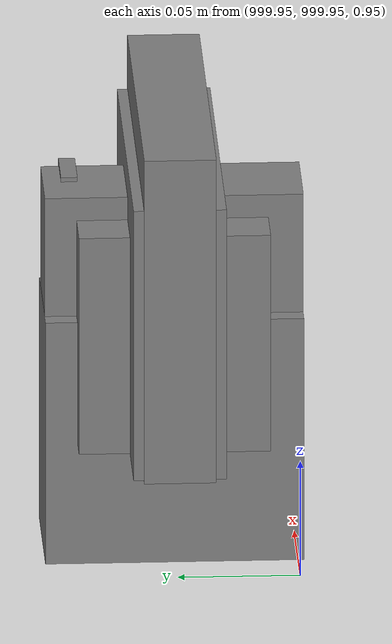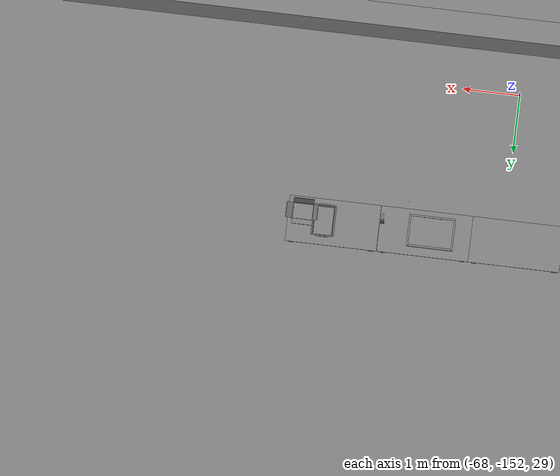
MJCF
<mujoco>
    <option gravity="0.000000000 0.000000000 -9.810000420" timestep="0.0049999999" integrator="implicitfast" density="1.225" viscosity="1.8000001e-05" noslip_iterations="10" iterations="100" sdf_iterations="50">
        <flag multiccd="disable"/>
    </option>
    <size memory="1000M"/>
    <compiler coordinate="local"/>
    <worldbody>
        <light cutoff="30" pos="0 1 1" dir="0 -1 -2"/>
        <light cutoff="30" pos="0 -1 1" dir="0 1 -2"/>
        <body pos="-65.872718811 -149.552307129 31.165109634" euler="35.810863495 -42.162322998 -39.206882477" mocap="true" name="spotlight5_SpotLight"/>
        <body pos="1000.000000000 1000.000000000 1.000000000" euler="0.000000000 0.000000000 180.000000000" name="openloong_gripper_2f85_fix_base_usda_battery_01">
            <geom contype="1" conaffinity="1" density="1000" type="box" material="" rgba="0.500000000 0.500000000 0.500000000 1.000000000" solimp="0.899999976 0.949999988 0.001000000" friction="1.000000000 0.005000000 0.000100000" solref="0.020000000 1.000000000" margin="0" condim="3" group="0" pos="-0.011123657 -0.041940309 0.101691343" quat="1.000000000 0.000000000 0.000000000 0.000000000" size="0.010800000 0.003375000 0.004725000" name="openloong_gripper_2f85_fix_base_usda_geom_4C5FD0E1_295D_405A_8BB9_75BAF0E1F83B"/>
            <geom contype="1" conaffinity="1" density="1000" type="box" material="" rgba="0.500000000 0.500000000 0.500000000 1.000000000" solimp="0.899999976 0.949999988 0.001000000" friction="1.000000000 0.005000000 0.000100000" solref="0.020000000 1.000000000" margin="0" condim="3" group="0" pos="-0.010876465 -0.044247437 0.047066893" quat="0.998702705 -0.050920475 0.000000000 0.000000000" size="0.009450001 0.002700000 0.024975000" name="openloong_gripper_2f85_fix_base_usda_geom_E8A9E434_9B0F_487F_B04C_75A126B8DF20"/>
            <geom contype="1" conaffinity="1" density="1000" type="box" material="" rgba="0.500000000 0.500000000 0.500000000 1.000000000" solimp="0.899999976 0.949999988 0.001000000" friction="1.000000000 0.005000000 0.000100000" solref="0.020000000 1.000000000" margin="0" condim="3" group="0" pos="-0.001235962 -0.000659180 0.047381196" quat="1.000000000 0.000000000 0.000000000 0.000000000" size="0.039420001 0.039150000 0.047250003" name="openloong_gripper_2f85_fix_base_usda_geom_422A4914_7B36_4A1E_88A5_2C6AB179424C"/>
            <geom contype="1" conaffinity="1" density="1000" type="box" material="" rgba="0.500000000 0.500000000 0.500000000 1.000000000" solimp="0.899999976 0.949999988 0.001000000" friction="1.000000000 0.005000000 0.000100000" solref="0.020000000 1.000000000" margin="0" condim="3" group="0" pos="-0.010876465 -0.039138794 0.009851727" quat="1.000000000 0.000000000 0.000000000 0.000000000" size="0.009450001 0.010800000 0.013500000" name="openloong_gripper_2f85_fix_base_usda_geom_39F8984F_B849_4370_BD4C_752786BC49FA"/>
            <geom contype="1" conaffinity="1" density="1000" type="box" material="" rgba="0.500000000 0.500000000 0.500000000 1.000000000" solimp="0.899999976 0.949999988 0.001000000" friction="1.000000000 0.005000000 0.000100000" solref="0.020000000 1.000000000" margin="0" condim="3" group="0" pos="-0.010876465 -0.041528322 0.071508206" quat="1.000000000 0.000000000 0.000000000 0.000000000" size="0.009450001 0.002700000 0.027000001" name="openloong_gripper_2f85_fix_base_usda_geom_E04E401E_814C_45E8_8D7A_997DFB4AFC5F"/>
            <freejoint name="openloong_gripper_2f85_fix_base_usda_battery_01_joint"/>
            <site size="0.005000000 0.005000000 0.005000000" rgba="0.500000000 0.500000000 0.500000000 1.000000000" pos="0.000000000 0.000000000 0.000000000" quat="0.999961913 0.008726500 0.000000000 0.000000000" group="0" type="sphere" name="openloong_gripper_2f85_fix_base_usda_battery_01site"/>
        </body>
        <body pos="-65.850967407 -148.907440186 31.170978546" euler="-91.327896118 14.244048119 57.318794250" mocap="true" name="spotlight6_SpotLight"/>
        <body pos="1000.000000000 1000.000000000 1.000000000" euler="0.000000000 0.000000000 180.000000000" name="openloong_gripper_2f85_fix_base_usda_wifi_box">
            <geom contype="1" conaffinity="1" density="1000" type="box" material="" rgba="0.500000000 0.500000000 0.500000000 1.000000000" solimp="0.899999976 0.949999988 0.001000000" friction="1.000000000 0.005000000 0.000100000" solref="0.020000000 1.000000000" margin="0" condim="3" group="0" pos="0.000000000 0.000000000 0.058978677" quat="0.000000000 0.000000047 0.000000000 1.000000000" size="0.068499997 0.018999999 0.059000000" name="openloong_gripper_2f85_fix_base_usda_geom_FBCB42FE_7DC3_4CDC_AEA6_3FEEF0B851DF"/>
            <freejoint name="openloong_gripper_2f85_fix_base_usda_wifi_box_joint"/>
            <site size="0.005000000 0.005000000 0.005000000" rgba="0.500000000 0.500000000 0.500000000 1.000000000" pos="0.000000000 0.000000000 0.000000000" quat="0.999961913 0.008726500 0.000000000 0.000000000" group="0" type="sphere" name="openloong_gripper_2f85_fix_base_usda_wifi_boxsite"/>
        </body>
        <body pos="1000.000000000 1000.000000000 1.000000000" euler="0.000000000 0.000000000 180.000000000" name="openloong_gripper_2f85_fix_base_usda_cpu_fan">
            <geom contype="1" conaffinity="1" density="1000" type="box" material="" rgba="0.500000000 0.500000000 0.500000000 1.000000000" solimp="0.899999976 0.949999988 0.001000000" friction="1.000000000 0.005000000 0.000100000" solref="0.020000000 1.000000000" margin="0" condim="3" group="0" pos="0.000000000 0.000000000 0.070034981" quat="0.000000000 0.000000000 0.000000000 1.000000000" size="0.070700005 0.014699999 0.070700005" name="openloong_gripper_2f85_fix_base_usda_geom_157B1313_A426_4A93_9400_39C517A99E1D"/>
            <freejoint name="openloong_gripper_2f85_fix_base_usda_cpu_fan_joint"/>
            <site size="0.005000000 0.005000000 0.005000000" rgba="0.500000000 0.500000000 0.500000000 1.000000000" pos="0.000000000 0.000000000 0.000000000" quat="0.999961913 0.008726535 0.000000000 0.000000000" group="0" type="sphere" name="openloong_gripper_2f85_fix_base_usda_cpu_fancsite"/>
        </body>
        <body pos="1000.000000000 1000.000000000 1.000000000" euler="0.000011953 0.000005123 -179.999984741" name="openloong_gripper_2f85_fix_base_usda_intel_box">
            <geom contype="1" conaffinity="1" density="1000" type="box" material="" rgba="0.500000000 0.500000000 0.500000000 1.000000000" solimp="0.899999976 0.949999988 0.001000000" friction="1.000000000 0.005000000 0.000100000" solref="0.020000000 1.000000000" margin="0" condim="3" group="0" pos="0.000000000 -0.000067139 0.000082284" quat="0.707106709 0.000000225 0.000000253 0.707106650" size="0.052800003 0.025300000 0.052800003" name="openloong_gripper_2f85_fix_base_usda_geom_CEF46439_9D3E_4DB0_8C74_1A82824983E9"/>
            <freejoint name="openloong_gripper_2f85_fix_base_usda_intel_box_joint"/>
            <site size="0.005000000 0.005000000 0.005000000" rgba="0.500000000 0.500000000 0.500000000 1.000000000" pos="0.000000000 0.000000000 0.000000000" quat="0.999961913 0.008726500 0.000000000 0.000000000" group="0" type="sphere" name="openloong_gripper_2f85_fix_base_usda_intel_boxsite"/>
        </body>
        <body pos="1000.000000000 999.999938965 1.000000000" euler="0.000000000 0.000000000 180.000000000" name="openloong_gripper_2f85_fix_base_usda_intelcore_i5">
            <geom contype="1" conaffinity="1" density="1000" type="box" material="" rgba="0.500000000 0.500000000 0.500000000 1.000000000" solimp="0.899999976 0.949999988 0.001000000" friction="1.000000000 0.005000000 0.000100000" solref="0.020000000 1.000000000" margin="0" condim="3" group="0" pos="0.000000000 0.000000000 0.051722717" quat="0.707106709 0.000000000 0.000000000 -0.707106769" size="0.052800000 0.018080002 0.052800000" name="openloong_gripper_2f85_fix_base_usda_geom_8EB31340_8873_4070_B1CF_3871AB50D126"/>
            <freejoint name="openloong_gripper_2f85_fix_base_usda_intelcore_i5_joint"/>
            <site size="0.005000000 0.005000000 0.005000000" rgba="0.500000000 0.500000000 0.500000000 1.000000000" pos="0.000000000 0.000000000 0.000000000" quat="0.999961913 0.008726534 0.000000000 0.000000000" group="0" type="sphere" name="openloong_gripper_2f85_fix_base_usda_intelcore_i5site"/>
        </body>
        <body pos="-66.393562317 -149.597747803 31.171993256" euler="90.759407043 52.279640198 -10.596117973" mocap="true" name="spotlight4_SpotLight"/>
        <body pos="-64.866622925 -149.383972168 30.183746338" euler="89.999984741 89.999946594 0.000000000" name="openloong_gripper_2f85_fix_base_usda_bluebox_01">
            <geom contype="1" conaffinity="1" density="1000" type="box" material="" rgba="0.500000000 0.500000000 0.500000000 1.000000000" solimp="0.899999976 0.949999988 0.001000000" friction="1.000000000 0.005000000 0.000100000" solref="0.020000000 1.000000000" margin="0" condim="3" group="0" pos="0.276580811 0.187225342 0.000068665" quat="0.707106948 0.000077471 0.707106352 0.000077486" size="0.100000001 0.057999998 0.010000000" name="openloong_gripper_2f85_fix_base_usda_geom_35AC4CAA_76E3_48B1_92DC_D50D65291B06"/>
            <geom contype="1" conaffinity="1" density="1000" type="box" material="" rgba="0.500000000 0.500000000 0.500000000 1.000000000" solimp="0.899999976 0.949999988 0.001000000" friction="1.000000000 0.005000000 0.000100000" solref="0.020000000 1.000000000" margin="0" condim="3" group="0" pos="0.000000000 0.002883911 0.000000000" quat="0.999999881 0.000000000 0.000000000 0.000000000" size="0.254000008 0.003000000 0.172000006" name="openloong_gripper_2f85_fix_base_usda_geom_16B679B2_C5C0_479E_9F95_1367BBF44CE7"/>
            <geom contype="1" conaffinity="1" density="1000" type="box" material="" rgba="0.500000000 0.500000000 0.500000000 1.000000000" solimp="0.899999976 0.949999988 0.001000000" friction="1.000000000 0.005000000 0.000100000" solref="0.020000000 1.000000000" margin="0" condim="3" group="0" pos="0.000000000 0.124874115 0.173484802" quat="0.999796331 0.020176515 -0.000000015 0.000000030" size="0.259999990 0.119999997 0.007000000" name="openloong_gripper_2f85_fix_base_usda_geom_1681A58D_2FB2_4D15_BB5D_2E0ACB78857F"/>
            <geom contype="1" conaffinity="1" density="1000" type="box" material="" rgba="0.500000000 0.500000000 0.500000000 1.000000000" solimp="0.899999976 0.949999988 0.001000000" friction="1.000000000 0.005000000 0.000100000" solref="0.020000000 1.000000000" margin="0" condim="3" group="0" pos="0.000000000 0.124874115 -0.173469543" quat="0.999796331 -0.020176545 -0.000000015 0.000000000" size="0.259999990 0.119999997 0.007000000" name="openloong_gripper_2f85_fix_base_usda_geom_879D2429_1580_4EE0_AFA6_CA287D1C92FC"/>
            <geom contype="1" conaffinity="1" density="1000" type="box" material="" rgba="0.500000000 0.500000000 0.500000000 1.000000000" solimp="0.899999976 0.949999988 0.001000000" friction="1.000000000 0.005000000 0.000100000" solref="0.020000000 1.000000000" margin="0" condim="3" group="0" pos="0.000000000 0.214008331 0.188980103" quat="0.999912977 0.013176724 0.000000015 0.000000000" size="0.259999990 0.029999999 0.012500000" name="openloong_gripper_2f85_fix_base_usda_geom_238447C8_FCDB_4A3E_9BF6_E97D8CD03D07"/>
            <geom contype="1" conaffinity="1" density="1000" type="box" material="" rgba="0.500000000 0.500000000 0.500000000 1.000000000" solimp="0.899999976 0.949999988 0.001000000" friction="1.000000000 0.005000000 0.000100000" solref="0.020000000 1.000000000" margin="0" condim="3" group="0" pos="-0.258361816 0.125289917 0.001876831" quat="0.702796936 -0.020792112 0.710783124 0.020769298" size="0.189999998 0.119999997 0.009000000" name="openloong_gripper_2f85_fix_base_usda_geom_EFF5E694_1449_4137_B59F_5A7DB8F495FD"/>
            <geom contype="1" conaffinity="1" density="1000" type="box" material="" rgba="0.500000000 0.500000000 0.500000000 1.000000000" solimp="0.899999976 0.949999988 0.001000000" friction="1.000000000 0.005000000 0.000100000" solref="0.020000000 1.000000000" margin="0" condim="3" group="0" pos="0.000000000 0.214008331 -0.188980103" quat="0.999912977 -0.013176769 0.000000030 0.000000015" size="0.259999990 0.029999999 0.012500000" name="openloong_gripper_2f85_fix_base_usda_geom_C4EAC9F8_0405_4812_B9DD_403785D86DC2"/>
            <geom contype="1" conaffinity="1" density="1000" type="box" material="" rgba="0.500000000 0.500000000 0.500000000 1.000000000" solimp="0.899999976 0.949999988 0.001000000" friction="1.000000000 0.005000000 0.000100000" solref="0.020000000 1.000000000" margin="0" condim="3" group="0" pos="-0.276611328 0.187225342 0.000068665" quat="0.707106650 0.000077441 0.707106709 0.000077456" size="0.100000001 0.057999998 0.010000000" name="openloong_gripper_2f85_fix_base_usda_geom_61F6DB82_A25A_4527_ADE8_9F0B91093812"/>
            <geom contype="1" conaffinity="1" density="1000" type="box" material="" rgba="0.500000000 0.500000000 0.500000000 1.000000000" solimp="0.899999976 0.949999988 0.001000000" friction="1.000000000 0.005000000 0.000100000" solref="0.020000000 1.000000000" margin="0" condim="3" group="0" pos="0.258331299 0.125289917 0.001876831" quat="0.702851415 0.018856421 0.710823774 -0.019329369" size="0.189999998 0.119999997 0.009000000" name="openloong_gripper_2f85_fix_base_usda_geom_520166B3_58D1_4ADE_B3EF_34EB64433A06"/>
            <freejoint name="openloong_gripper_2f85_fix_base_usda_bluebox_01_joint"/>
            <site size="0.005000000 0.005000000 0.005000000" rgba="0.500000000 0.500000000 0.500000000 1.000000000" pos="0.000000000 0.000000000 0.000000000" quat="0.999961913 0.008726534 0.000000000 0.000000000" group="0" type="sphere" name="openloong_gripper_2f85_fix_base_usda_bluebox_01site"/>
        </body>
        <body pos="-64.496299744 -149.491867065 30.235729218" euler="0.000000000 0.000000000 89.999946594" name="openloong_gripper_2f85_fix_base_usda_cardboardbox_01">
            <geom contype="1" conaffinity="1" density="1000" type="box" material="" rgba="0.500000000 0.500000000 0.500000000 1.000000000" solimp="0.899999976 0.949999988 0.001000000" friction="1.000000000 0.005000000 0.000100000" solref="0.020000000 1.000000000" margin="0" condim="3" group="0" pos="-0.003166199 -0.004086494 0.005052090" quat="1.000000000 0.000000000 0.000000000 0.000000000" size="0.142499998 0.177500010 0.005000000" name="openloong_gripper_2f85_fix_base_usda_geom_9EB9B7A2_42EF_43AF_9766_F190CE840BBE"/>
            <geom contype="1" conaffinity="1" density="1000" type="box" material="" rgba="0.500000000 0.500000000 0.500000000 1.000000000" solimp="0.899999976 0.949999988 0.001000000" friction="1.000000000 0.005000000 0.000100000" solref="0.020000000 1.000000000" margin="0" condim="3" group="0" pos="-0.003166199 0.170316696 0.150570869" quat="1.000000000 0.000000000 0.000000000 0.000000000" size="0.142499998 0.005000000 0.149999991" name="openloong_gripper_2f85_fix_base_usda_geom_15606F8A_A207_42D1_9C40_754DE212D80C"/>
            <geom contype="1" conaffinity="1" density="1000" type="box" material="" rgba="0.500000000 0.500000000 0.500000000 1.000000000" solimp="0.899999976 0.949999988 0.001000000" friction="1.000000000 0.005000000 0.000100000" solref="0.020000000 1.000000000" margin="0" condim="3" group="0" pos="-0.147399902 -0.005307198 0.150570869" quat="1.000000000 0.000000000 0.000000000 0.000000000" size="0.005000000 0.177500010 0.149999991" name="openloong_gripper_2f85_fix_base_usda_geom_DE667A85_1342_4676_A813_2D232CAF2BD3"/>
            <geom contype="1" conaffinity="1" density="1000" type="box" material="" rgba="0.500000000 0.500000000 0.500000000 1.000000000" solimp="0.899999976 0.949999988 0.001000000" friction="1.000000000 0.005000000 0.000100000" solref="0.020000000 1.000000000" margin="0" condim="3" group="0" pos="0.140275955 -0.005307198 0.150570869" quat="1.000000000 0.000000000 0.000000000 0.000000000" size="0.005000000 0.177500010 0.149999991" name="openloong_gripper_2f85_fix_base_usda_geom_3F2B1CF6_9292_4922_82A5_651CECF00B83"/>
            <geom contype="1" conaffinity="1" density="1000" type="box" material="" rgba="0.500000000 0.500000000 0.500000000 1.000000000" solimp="0.899999976 0.949999988 0.001000000" friction="1.000000000 0.005000000 0.000100000" solref="0.020000000 1.000000000" margin="0" condim="3" group="0" pos="-0.003166199 -0.181550980 0.150570869" quat="1.000000000 0.000000000 0.000000000 0.000000000" size="0.142499998 0.005000000 0.149999991" name="openloong_gripper_2f85_fix_base_usda_geom_45E2FABE_826C_4F09_AB05_43DCA84F3733"/>
            <freejoint name="openloong_gripper_2f85_fix_base_usda_cardboardbox_01_joint"/>
            <site size="0.005000000 0.005000000 0.005000000" rgba="0.500000000 0.500000000 0.500000000 1.000000000" pos="0.000000000 0.000000000 0.000000000" quat="0.999961913 0.008726535 0.000000000 0.000000000" group="0" type="sphere" name="openloong_gripper_2f85_fix_base_usda_site_EA66D5B8_87EB_4618_AAC1_52C43A4AC35F"/>
            <body pos="0.139160156 -0.004048347 0.301930904" euler="-179.999954224 49.383502960 179.999954224" name="openloong_gripper_2f85_fix_base_usda_A1_006">
                <geom contype="1" conaffinity="1" density="1000" type="box" material="" rgba="0.500000000 0.500000000 0.500000000 1.000000000" solimp="0.899999976 0.949999988 0.001000000" friction="1.000000000 0.005000000 0.000100000" solref="0.020000000 1.000000000" margin="0" condim="3" group="0" pos="-0.071587563 0.000009537 0.001745224" quat="0.999999881 0.000000000 0.000000000 0.000000000" size="0.071249999 0.179999992 0.002500000" name="openloong_gripper_2f85_fix_base_usda_geom_7E48F0FD_77A1_49A6_A523_4A39AE2D64DD"/>
                <joint armature="0" stiffness="0.07" damping="0.0099999998" axis="0.000000 1.000000 0.000000" type="hinge" name="openloong_gripper_2f85_fix_base_usda_A1_006"/>
            </body>
            <body pos="-0.145902634 -0.004086494 0.301938057" euler="-180.000000000 -60.000011444 -180.000000000" name="openloong_gripper_2f85_fix_base_usda_A2_006">
                <geom contype="1" conaffinity="1" density="1000" type="box" material="" rgba="0.500000000 0.500000000 0.500000000 1.000000000" solimp="0.899999976 0.949999988 0.001000000" friction="1.000000000 0.005000000 0.000100000" solref="0.020000000 1.000000000" margin="0" condim="3" group="0" pos="0.071268082 0.000009537 0.002717972" quat="0.000002921 0.000000000 -0.000000030 0.999999881" size="0.071249999 0.179999992 0.002500000" name="openloong_gripper_2f85_fix_base_usda_geom_F5551CF4_A3EE_4434_8D60_C880F8B633FD"/>
                <joint armature="0" stiffness="0.07" damping="0.0099999998" axis="0.000000 1.000000 0.000000" type="hinge" name="openloong_gripper_2f85_fix_base_usda_A2_006"/>
            </body>
            <body pos="-0.003385544 0.175991058 0.301930904" euler="-125.858116150 -0.000004561 0.000002331" name="openloong_gripper_2f85_fix_base_usda_B2_006">
                <geom contype="1" conaffinity="1" density="1000" type="box" material="" rgba="0.500000000 0.500000000 0.500000000 1.000000000" solimp="0.899999976 0.949999988 0.001000000" friction="1.000000000 0.005000000 0.000100000" solref="0.020000000 1.000000000" margin="0" condim="3" group="0" pos="0.000009537 -0.070939064 -0.002470016" quat="0.999614120 0.027776197 -0.000000015 0.000000030" size="0.137500003 0.064999998 0.005000000" name="openloong_gripper_2f85_fix_base_usda_geom_C72EBDA0_8DC7_448E_8D1F_9C29F82690A6"/>
                <joint armature="0" stiffness="0.07" damping="0.0099999998" axis="1.000000 0.000000 0.000000" type="hinge" name="openloong_gripper_2f85_fix_base_usda_B2_006"/>
            </body>
            <body pos="-0.003385544 -0.184140205 0.301938057" euler="147.805557251 0.000000000 0.000000000" name="openloong_gripper_2f85_fix_base_usda_B1_006">
                <geom contype="1" conaffinity="1" density="1000" type="box" material="" rgba="0.500000000 0.500000000 0.500000000 1.000000000" solimp="0.899999976 0.949999988 0.001000000" friction="1.000000000 0.005000000 0.000100000" solref="0.020000000 1.000000000" margin="0" condim="3" group="0" pos="-0.000028610 0.070202351 -0.002703667" quat="0.999614179 -0.027776167 0.000000000 0.000000000" size="0.137500003 0.064999998 0.005000000" name="openloong_gripper_2f85_fix_base_usda_geom_AD94DF55_F1F7_47EE_8847_F80075E66002"/>
                <joint armature="0" stiffness="0.07" damping="0.0099999998" axis="1.000000 0.000000 0.000000" type="hinge" name="openloong_gripper_2f85_fix_base_usda_B1_006"/>
            </body>
        </body>
        <body pos="-65.882858276 -149.481979370 30.229999542" euler="-64.487716675 0.000000000 0.000000000" name="openloong_gripper_2f85_fix_base_usda_Barcode">
            <geom contype="1" conaffinity="1" density="1000" type="box" material="" rgba="0.500000000 0.500000000 0.500000000 1.000000000" solimp="0.899999976 0.949999988 0.001000000" friction="1.000000000 0.005000000 0.000100000" solref="0.020000000 1.000000000" margin="0" condim="3" group="0" pos="0.000000000 0.013038635 0.001419067" quat="0.000000000 0.000000000 0.000000000 1.000000119" size="0.034000002 0.010000000 0.017999999" name="openloong_gripper_2f85_fix_base_usda_geom_6B91CB6F_14A2_420D_9A6D_5A908CA7C0FD"/>
            <geom contype="1" conaffinity="1" density="1000" type="box" material="" rgba="0.500000000 0.500000000 0.500000000 1.000000000" solimp="0.899999976 0.949999988 0.001000000" friction="1.000000000 0.005000000 0.000100000" solref="0.020000000 1.000000000" margin="0" condim="3" group="0" pos="0.000000000 -0.035301208 -0.007095337" quat="0.000000000 0.000000000 -0.043619365 0.999048233" size="0.028999999 0.010000000 0.020000000" name="openloong_gripper_2f85_fix_base_usda_geom_B1D1D415_A862_499E_92E2_F21978806992"/>
            <geom contype="1" conaffinity="1" density="1000" type="box" material="" rgba="0.500000000 0.500000000 0.500000000 1.000000000" solimp="0.899999976 0.949999988 0.001000000" friction="1.000000000 0.005000000 0.000100000" solref="0.020000000 1.000000000" margin="0" condim="3" group="0" pos="0.000000000 -0.043411255 -0.011749268" quat="0.922262907 0.386563420 0.000000000 0.000000000" size="0.026000001 0.010000000 0.020000000" name="openloong_gripper_2f85_fix_base_usda_geom_8B63A11B_1156_47EB_B341_B0E8FC6C76F6"/>
            <geom contype="1" conaffinity="1" density="1000" type="box" material="" rgba="0.500000000 0.500000000 0.500000000 1.000000000" solimp="0.899999976 0.949999988 0.001000000" friction="1.000000000 0.005000000 0.000100000" solref="0.020000000 1.000000000" margin="0" condim="3" group="0" pos="0.000000000 -0.016967773 -0.031860352" quat="0.000000000 0.000000000 0.000000000 1.000000119" size="0.008000000 0.010000000 0.013000000" name="openloong_gripper_2f85_fix_base_usda_geom_4F24F9A1_4912_4AC3_A9B8_5ECB5A7BAF75"/>
            <geom contype="1" conaffinity="1" density="1000" type="box" material="" rgba="0.500000000 0.500000000 0.500000000 1.000000000" solimp="0.899999976 0.949999988 0.001000000" friction="1.000000000 0.005000000 0.000100000" solref="0.020000000 1.000000000" margin="0" condim="3" group="0" pos="0.000000000 -0.001869202 0.000312805" quat="0.953716993 0.300705761 0.000000000 0.000000000" size="0.032000002 0.010000000 0.018999999" name="openloong_gripper_2f85_fix_base_usda_geom_FEE1D892_148B_4675_8ABE_6EA01C916EDE"/>
            <geom contype="1" conaffinity="1" density="1000" type="box" material="" rgba="0.500000000 0.500000000 0.500000000 1.000000000" solimp="0.899999976 0.949999988 0.001000000" friction="1.000000000 0.005000000 0.000100000" solref="0.020000000 1.000000000" margin="0" condim="3" group="0" pos="0.000000000 -0.019531250 -0.003173828" quat="0.953716993 0.300705761 0.000000000 0.000000000" size="0.030999999 0.010000000 0.020000000" name="openloong_gripper_2f85_fix_base_usda_geom_73C36193_74B9_4B0F_9166_0399352DE81A"/>
            <geom contype="1" conaffinity="1" density="1000" type="box" material="" rgba="0.500000000 0.500000000 0.500000000 1.000000000" solimp="0.899999976 0.949999988 0.001000000" friction="1.000000000 0.005000000 0.000100000" solref="0.020000000 1.000000000" margin="0" condim="3" group="0" pos="0.000000000 -0.035301208 -0.007095337" quat="0.953716993 0.300705761 0.000000000 0.000000000" size="0.028999999 0.010000000 0.020000000" name="openloong_gripper_2f85_fix_base_usda_geom_4FCD276A_A04D_4381_A956_DED0D379433C"/>
            <geom contype="1" conaffinity="1" density="1000" type="box" material="" rgba="0.500000000 0.500000000 0.500000000 1.000000000" solimp="0.899999976 0.949999988 0.001000000" friction="1.000000000 0.005000000 0.000100000" solref="0.020000000 1.000000000" margin="0" condim="3" group="0" pos="0.000000000 -0.042617798 -0.071121216" quat="0.000000000 0.000000000 0.000000000 1.000000119" size="0.013000000 0.021000000 0.059999999" name="openloong_gripper_2f85_fix_base_usda_geom_118E4EA2_3588_4F1A_BAEE_79F5597952FE"/>
            <freejoint name="openloong_gripper_2f85_fix_base_usda_Barcode_joint"/>
            <site size="0.005000000 0.005000000 0.005000000" rgba="0.500000000 0.500000000 0.500000000 1.000000000" pos="0.000000000 0.000000000 0.000000000" quat="1.000000000 0.000000000 0.000000000 0.000000000" group="0" type="sphere" name="openloong_gripper_2f85_fix_base_usda_Barcode_site"/>
        </body>
        <body pos="-66.745018005 -149.392349243 30.184000015" euler="0.000000000 0.000000000 89.999946594" name="[22331520673595]_Basket_01">
            <geom contype="1" conaffinity="1" density="1000" type="box" material="" rgba="0.500000000 0.500000000 0.500000000 1.000000000" solimp="0.899999976 0.949999988 0.001000000" friction="1.000000000 0.005000000 0.000100000" solref="0.020000000 1.000000000" margin="0" condim="3" group="0" pos="-0.052425385 0.389207840 0.089787483" quat="0.707107008 0.000000000 0.000000000 0.707106411" size="0.014249999 0.014249999 0.059999999" name="[22331520673595]_geom_14C86D5A_939B_498E_A010_E381F66B0A0E"/>
            <geom contype="1" conaffinity="1" density="1000" type="box" material="" rgba="0.500000000 0.500000000 0.500000000 1.000000000" solimp="0.899999976 0.949999988 0.001000000" friction="1.000000000 0.005000000 0.000100000" solref="0.020000000 1.000000000" margin="0" condim="3" group="0" pos="0.264015198 -0.133043289 0.089787483" quat="0.707107008 0.000000000 0.000000000 0.707106411" size="0.014249999 0.014249999 0.059999999" name="[22331520673595]_geom_91096FA6_309C_4B12_9D32_A54F53AB357C"/>
            <geom contype="1" conaffinity="1" density="1000" type="box" material="" rgba="0.500000000 0.500000000 0.500000000 1.000000000" solimp="0.899999976 0.949999988 0.001000000" friction="1.000000000 0.005000000 0.000100000" solref="0.020000000 1.000000000" margin="0" condim="3" group="0" pos="-0.264015198 -0.265548706 0.089793205" quat="0.707107008 0.000000000 0.000000000 0.707106411" size="0.014249999 0.014249999 0.059999999" name="[22331520673595]_geom_B99A12DA_4AB5_4DE6_BA11_154EE275BA37"/>
            <geom contype="1" conaffinity="1" density="1000" type="box" material="" rgba="0.500000000 0.500000000 0.500000000 1.000000000" solimp="0.899999976 0.949999988 0.001000000" friction="1.000000000 0.005000000 0.000100000" solref="0.020000000 1.000000000" margin="0" condim="3" group="0" pos="-0.160263062 -0.389322281 0.089793205" quat="0.707107008 0.000000000 0.000000000 0.707106411" size="0.014249999 0.014249999 0.059999999" name="[22331520673595]_geom_4585F8FD_4F61_4E43_B8DA_EB673E277344"/>
            <geom contype="1" conaffinity="1" density="1000" type="box" material="" rgba="0.500000000 0.500000000 0.500000000 1.000000000" solimp="0.899999976 0.949999988 0.001000000" friction="1.000000000 0.005000000 0.000100000" solref="0.020000000 1.000000000" margin="0" condim="3" group="0" pos="0.162265778 -0.389322281 0.089787483" quat="0.707107008 0.000000000 0.000000000 0.707106411" size="0.014249999 0.014249999 0.059999999" name="[22331520673595]_geom_9399934E_B8A2_4263_B064_B277DF183E17"/>
            <geom contype="1" conaffinity="1" density="1000" type="box" material="" rgba="0.500000000 0.500000000 0.500000000 1.000000000" solimp="0.899999976 0.949999988 0.001000000" friction="1.000000000 0.005000000 0.000100000" solref="0.020000000 1.000000000" margin="0" condim="3" group="0" pos="0.264015198 0.389207840 0.089787483" quat="0.707107008 0.000000000 0.000000000 0.707106411" size="0.014249999 0.014249999 0.059999999" name="[22331520673595]_geom_FE5AF8FC_4547_43BA_9DE8_B99160993434"/>
            <geom contype="1" conaffinity="1" density="1000" type="box" material="" rgba="0.500000000 0.500000000 0.500000000 1.000000000" solimp="0.899999976 0.949999988 0.001000000" friction="1.000000000 0.005000000 0.000100000" solref="0.020000000 1.000000000" margin="0" condim="3" group="0" pos="-0.264015198 -0.133043289 0.089793205" quat="0.707107008 0.000000000 0.000000000 0.707106411" size="0.014249999 0.014249999 0.059999999" name="[22331520673595]_geom_DA8D7B5E_63C1_44B8_A920_C27F4A57BA90"/>
            <geom contype="1" conaffinity="1" density="1000" type="box" material="" rgba="0.500000000 0.500000000 0.500000000 1.000000000" solimp="0.899999976 0.949999988 0.001000000" friction="1.000000000 0.005000000 0.000100000" solref="0.020000000 1.000000000" margin="0" condim="3" group="0" pos="-0.264026642 0.269256592 0.089793205" quat="0.707107008 0.000000000 0.000000000 0.707106411" size="0.014249999 0.014249999 0.059999999" name="[22331520673595]_geom_BCD4641B_81EE_40D1_A543_A5A279316D01"/>
            <geom contype="1" conaffinity="1" density="1000" type="box" material="" rgba="0.500000000 0.500000000 0.500000000 1.000000000" solimp="0.899999976 0.949999988 0.001000000" friction="1.000000000 0.005000000 0.000100000" solref="0.020000000 1.000000000" margin="0" condim="3" group="0" pos="0.054462433 0.389207840 0.089787483" quat="0.707107008 0.000000000 0.000000000 0.707106411" size="0.014249999 0.014249999 0.059999999" name="[22331520673595]_geom_DCD113EC_E298_4E3F_80FA_73EAE9640ADF"/>
            <geom contype="1" conaffinity="1" density="1000" type="box" material="" rgba="0.500000000 0.500000000 0.500000000 1.000000000" solimp="0.899999976 0.949999988 0.001000000" friction="1.000000000 0.005000000 0.000100000" solref="0.020000000 1.000000000" margin="0" condim="3" group="0" pos="0.054462433 -0.389322281 0.089787483" quat="0.707107008 0.000000000 0.000000000 0.707106411" size="0.014249999 0.014249999 0.059999999" name="[22331520673595]_geom_9A6C0A66_6256_4D75_B856_D1DF3C18CB86"/>
            <geom contype="1" conaffinity="1" density="1000" type="box" material="" rgba="0.500000000 0.500000000 0.500000000 1.000000000" solimp="0.899999976 0.949999988 0.001000000" friction="1.000000000 0.005000000 0.000100000" solref="0.020000000 1.000000000" margin="0" condim="3" group="0" pos="0.264015198 0.269256592 0.089793205" quat="0.707107008 0.000000000 0.000000000 0.707106411" size="0.014249999 0.014249999 0.059999999" name="[22331520673595]_geom_8AF068FC_27AF_4F63_A376_5B12C5880D51"/>
            <geom contype="1" conaffinity="1" density="1000" type="box" material="" rgba="0.500000000 0.500000000 0.500000000 1.000000000" solimp="0.899999976 0.949999988 0.001000000" friction="1.000000000 0.005000000 0.000100000" solref="0.020000000 1.000000000" margin="0" condim="3" group="0" pos="0.264015198 -0.389322281 0.089787483" quat="0.707107008 0.000000000 0.000000000 0.707106411" size="0.014249999 0.014249999 0.059999999" name="[22331520673595]_geom_2A219BE9_A12B_4675_B2EF_46DDA151820F"/>
            <geom contype="1" conaffinity="1" density="1000" type="box" material="" rgba="0.500000000 0.500000000 0.500000000 1.000000000" solimp="0.899999976 0.949999988 0.001000000" friction="1.000000000 0.005000000 0.000100000" solref="0.020000000 1.000000000" margin="0" condim="3" group="0" pos="0.000000000 0.000000000 0.015998840" quat="0.707107008 0.000000000 0.000000000 0.707106411" size="0.403499991 0.279000014 0.015750000" name="[22331520673595]_geom_F66A9B21_F824_46D2_9787_7F12180CC732"/>
            <geom contype="1" conaffinity="1" density="1000" type="box" material="" rgba="0.500000000 0.500000000 0.500000000 1.000000000" solimp="0.899999976 0.949999988 0.001000000" friction="1.000000000 0.005000000 0.000100000" solref="0.020000000 1.000000000" margin="0" condim="3" group="0" pos="0.000000000 -0.389476776 0.163619041" quat="0.707107008 0.000000000 0.000000000 0.707106411" size="0.015000000 0.277500004 0.015750000" name="[22331520673595]_geom_609FD927_6B72_450F_9AEE_307496EAD676"/>
            <geom contype="1" conaffinity="1" density="1000" type="box" material="" rgba="0.500000000 0.500000000 0.500000000 1.000000000" solimp="0.899999976 0.949999988 0.001000000" friction="1.000000000 0.005000000 0.000100000" solref="0.020000000 1.000000000" margin="0" condim="3" group="0" pos="0.162265778 0.389207840 0.089787483" quat="0.707107008 0.000000000 0.000000000 0.707106411" size="0.014249999 0.014249999 0.059999999" name="[22331520673595]_geom_9EA75826_7B97_4A9C_8601_57E0E7DE5844"/>
            <geom contype="1" conaffinity="1" density="1000" type="box" material="" rgba="0.500000000 0.500000000 0.500000000 1.000000000" solimp="0.899999976 0.949999988 0.001000000" friction="1.000000000 0.005000000 0.000100000" solref="0.020000000 1.000000000" margin="0" condim="3" group="0" pos="0.000000000 0.389471054 0.163619041" quat="0.707107008 0.000000000 0.000000000 0.707106411" size="0.015000000 0.277500004 0.015750000" name="[22331520673595]_geom_F1A4C72D_1330_4769_84C7_2537A83946E1"/>
            <geom contype="1" conaffinity="1" density="1000" type="box" material="" rgba="0.500000000 0.500000000 0.500000000 1.000000000" solimp="0.899999976 0.949999988 0.001000000" friction="1.000000000 0.005000000 0.000100000" solref="0.020000000 1.000000000" margin="0" condim="3" group="0" pos="-0.263511658 0.000000000 0.163619041" quat="0.707107008 0.000000000 0.000000000 0.707106411" size="0.403499991 0.015000000 0.015750000" name="[22331520673595]_geom_E8AD2D29_3B9E_4CEA_A88E_E96C6AD4245D"/>
            <geom contype="1" conaffinity="1" density="1000" type="box" material="" rgba="0.500000000 0.500000000 0.500000000 1.000000000" solimp="0.899999976 0.949999988 0.001000000" friction="1.000000000 0.005000000 0.000100000" solref="0.020000000 1.000000000" margin="0" condim="3" group="0" pos="-0.264015198 0.141334534 0.089793205" quat="0.707107008 0.000000000 0.000000000 0.707106411" size="0.014249999 0.014249999 0.059999999" name="[22331520673595]_geom_51D35BE7_F921_49C5_9A4B_D50B80F9FB70"/>
            <geom contype="1" conaffinity="1" density="1000" type="box" material="" rgba="0.500000000 0.500000000 0.500000000 1.000000000" solimp="0.899999976 0.949999988 0.001000000" friction="1.000000000 0.005000000 0.000100000" solref="0.020000000 1.000000000" margin="0" condim="3" group="0" pos="0.264015198 -0.265548706 0.089787483" quat="0.707107008 0.000000000 0.000000000 0.707106411" size="0.014249999 0.014249999 0.059999999" name="[22331520673595]_geom_E56D95FC_7EBA_4AA1_9125_06316E8E72A3"/>
            <geom contype="1" conaffinity="1" density="1000" type="box" material="" rgba="0.500000000 0.500000000 0.500000000 1.000000000" solimp="0.899999976 0.949999988 0.001000000" friction="1.000000000 0.005000000 0.000100000" solref="0.020000000 1.000000000" margin="0" condim="3" group="0" pos="-0.160263062 0.389207840 0.089787483" quat="0.707107008 0.000000000 0.000000000 0.707106411" size="0.014249999 0.014249999 0.059999999" name="[22331520673595]_geom_A57076BA_4D62_4A23_8217_382D89F61CFE"/>
            <geom contype="1" conaffinity="1" density="1000" type="box" material="" rgba="0.500000000 0.500000000 0.500000000 1.000000000" solimp="0.899999976 0.949999988 0.001000000" friction="1.000000000 0.005000000 0.000100000" solref="0.020000000 1.000000000" margin="0" condim="3" group="0" pos="-0.052425385 -0.389322281 0.089787483" quat="0.707107008 0.000000000 0.000000000 0.707106411" size="0.014249999 0.014249999 0.059999999" name="[22331520673595]_geom_C93AFE18_BA0F_4F69_9408_B855F9F7EDD1"/>
            <geom contype="1" conaffinity="1" density="1000" type="box" material="" rgba="0.500000000 0.500000000 0.500000000 1.000000000" solimp="0.899999976 0.949999988 0.001000000" friction="1.000000000 0.005000000 0.000100000" solref="0.020000000 1.000000000" margin="0" condim="3" group="0" pos="-0.264026642 -0.389322281 0.089793205" quat="0.707107008 0.000000000 0.000000000 0.707106411" size="0.014249999 0.014249999 0.059999999" name="[22331520673595]_geom_5E51B6C1_1924_460E_BA39_A8E29281665F"/>
            <geom contype="1" conaffinity="1" density="1000" type="box" material="" rgba="0.500000000 0.500000000 0.500000000 1.000000000" solimp="0.899999976 0.949999988 0.001000000" friction="1.000000000 0.005000000 0.000100000" solref="0.020000000 1.000000000" margin="0" condim="3" group="0" pos="0.264015198 0.141334534 0.089787483" quat="0.707107008 0.000000000 0.000000000 0.707106411" size="0.014249999 0.014249999 0.059999999" name="[22331520673595]_geom_A32B042D_07B5_459F_85C9_1C10D8555ECE"/>
            <geom contype="1" conaffinity="1" density="1000" type="box" material="" rgba="0.500000000 0.500000000 0.500000000 1.000000000" solimp="0.899999976 0.949999988 0.001000000" friction="1.000000000 0.005000000 0.000100000" solref="0.020000000 1.000000000" margin="0" condim="3" group="0" pos="-0.264015198 0.389207840 0.089793205" quat="0.707107008 0.000000000 0.000000000 0.707106411" size="0.014249999 0.014249999 0.059999999" name="[22331520673595]_geom_07570735_A3D1_478D_B02E_FAA7ABE7B4C1"/>
            <geom contype="1" conaffinity="1" density="1000" type="box" material="" rgba="0.500000000 0.500000000 0.500000000 1.000000000" solimp="0.899999976 0.949999988 0.001000000" friction="1.000000000 0.005000000 0.000100000" solref="0.020000000 1.000000000" margin="0" condim="3" group="0" pos="0.264015198 0.004480362 0.089787483" quat="0.707107008 0.000000000 0.000000000 0.707106411" size="0.014249999 0.014249999 0.059999999" name="[22331520673595]_geom_E9FB09DE_F218_45CC_9670_0980A34FB690"/>
            <geom contype="1" conaffinity="1" density="1000" type="box" material="" rgba="0.500000000 0.500000000 0.500000000 1.000000000" solimp="0.899999976 0.949999988 0.001000000" friction="1.000000000 0.005000000 0.000100000" solref="0.020000000 1.000000000" margin="0" condim="3" group="0" pos="0.263694763 -0.000011444 0.163619041" quat="0.707107008 0.000000000 0.000000000 0.707106411" size="0.403499991 0.015000000 0.015750000" name="[22331520673595]_geom_8EC5F8F7_EDAC_4303_BF45_E6588A46860A"/>
            <geom contype="1" conaffinity="1" density="1000" type="box" material="" rgba="0.500000000 0.500000000 0.500000000 1.000000000" solimp="0.899999976 0.949999988 0.001000000" friction="1.000000000 0.005000000 0.000100000" solref="0.020000000 1.000000000" margin="0" condim="3" group="0" pos="-0.264015198 0.004480362 0.089793205" quat="0.707107008 0.000000000 0.000000000 0.707106411" size="0.014249999 0.014249999 0.059999999" name="[22331520673595]_geom_5079E37C_F66F_4FBC_9DCC_1BAD0D294647"/>
            <freejoint name="[22331520673595]_joint_D70A8003_CDDB_43BE_B621_52C196E20E46"/>
        </body>
        <body pos="0.000000000 0.000000000 0.000000000" euler="0.000000000 0.000000000 0.000000000" name="Static Objects_Static Objects">
            <geom contype="1" conaffinity="1" density="1000" type="box" material="" rgba="0.500000000 0.500000000 0.500000000 1.000000000" solimp="0.899999976 0.949999988 0.001000000" friction="1.000000000 0.005000000 0.000100000" solref="0.020000000 1.000000000" margin="0" condim="3" group="0" pos="-67.544113159 -149.365814209 29.727830887" quat="0.500000417 0.499999970 0.499999553 0.499999970" size="0.381000012 0.319999993 0.041000001" name="Static Objects_geom_CE95BA0F_D762_4B33_A5B2_41EC855A6D5E"/>
            <geom contype="1" conaffinity="1" density="1000" type="box" material="" rgba="0.500000000 0.500000000 0.500000000 1.000000000" solimp="0.899999976 0.949999988 0.001000000" friction="1.000000000 0.005000000 0.000100000" solref="0.020000000 1.000000000" margin="0" condim="3" group="0" pos="-68.239501953 -149.365814209 30.086868286" quat="0.500000417 0.499999970 0.499999553 0.499999970" size="0.370999992 0.039500002 0.745000005" name="Static Objects_geom_0F825AEE_339D_41DD_B62F_35D1496AAEDF"/>
            <geom contype="1" conaffinity="1" density="1000" type="box" material="" rgba="0.500000000 0.500000000 0.500000000 1.000000000" solimp="0.899999976 0.949999988 0.001000000" friction="1.000000000 0.005000000 0.000100000" solref="0.020000000 1.000000000" margin="0" condim="3" group="0" pos="-68.239501953 -149.365814209 30.147235870" quat="0.500000417 0.499999970 0.499999553 0.499999970" size="0.400000006 0.022000000 0.800000012" name="Static Objects_geom_3EFBCBDD_3452_4FA4_B815_18E6042119E7"/>
            <geom contype="1" conaffinity="1" density="1000" type="box" material="" rgba="0.500000000 0.500000000 0.500000000 1.000000000" solimp="0.899999976 0.949999988 0.001000000" friction="1.000000000 0.005000000 0.000100000" solref="0.020000000 1.000000000" margin="0" condim="3" group="0" pos="-68.934890747 -149.365814209 29.727830887" quat="0.500000417 0.499999970 0.499999553 0.499999970" size="0.381000012 0.319999993 0.041000001" name="Static Objects_geom_7768BBE4_04F2_49EB_82D1_8DB92C6428E3"/>
            <geom contype="1" conaffinity="1" density="1000" type="box" material="" rgba="0.500000000 0.500000000 0.500000000 1.000000000" solimp="0.899999976 0.949999988 0.001000000" friction="1.000000000 0.005000000 0.000100000" solref="0.020000000 1.000000000" margin="0" condim="3" group="0" pos="-68.239501953 -149.365814209 29.561563492" quat="0.500000417 0.499999970 0.499999553 0.499999970" size="0.020000000 0.022000000 0.660000026" name="Static Objects_geom_BFC440DD_5165_4A4D_8FA8_29D53EB0C599"/>
            <geom contype="1" conaffinity="1" density="1000" type="box" material="" rgba="0.500000000 0.500000000 0.500000000 1.000000000" solimp="0.899999976 0.949999988 0.001000000" friction="1.000000000 0.005000000 0.000100000" solref="0.020000000 1.000000000" margin="0" condim="3" group="0" pos="-65.945671082 -149.365814209 29.727830887" quat="0.500000417 0.499999970 0.499999553 0.499999970" size="0.381000012 0.319999993 0.041000001" name="Static Objects_geom_0577032F_76D4_4686_AAA4_3705244F306E"/>
            <geom contype="1" conaffinity="1" density="1000" type="box" material="" rgba="0.500000000 0.500000000 0.500000000 1.000000000" solimp="0.899999976 0.949999988 0.001000000" friction="1.000000000 0.005000000 0.000100000" solref="0.020000000 1.000000000" margin="0" condim="3" group="0" pos="-66.641059875 -149.365814209 30.086868286" quat="0.500000417 0.499999970 0.499999553 0.499999970" size="0.370999992 0.039500002 0.745000005" name="Static Objects_geom_917FE52F_69D7_4034_A235_26FBB1C10B42"/>
            <geom contype="1" conaffinity="1" density="1000" type="box" material="" rgba="0.500000000 0.500000000 0.500000000 1.000000000" solimp="0.899999976 0.949999988 0.001000000" friction="1.000000000 0.005000000 0.000100000" solref="0.020000000 1.000000000" margin="0" condim="3" group="0" pos="-66.641059875 -149.365814209 30.147235870" quat="0.500000417 0.499999970 0.499999553 0.499999970" size="0.400000006 0.022000000 0.800000012" name="Static Objects_geom_43698335_6B82_4ABA_9042_D0BA04A9A3C7"/>
            <geom contype="1" conaffinity="1" density="1000" type="box" material="" rgba="0.500000000 0.500000000 0.500000000 1.000000000" solimp="0.899999976 0.949999988 0.001000000" friction="1.000000000 0.005000000 0.000100000" solref="0.020000000 1.000000000" margin="0" condim="3" group="0" pos="-67.336448669 -149.365814209 29.727830887" quat="0.500000417 0.499999970 0.499999553 0.499999970" size="0.381000012 0.319999993 0.041000001" name="Static Objects_geom_6DDB5FF9_9C08_48AA_840C_73538C61DF86"/>
            <geom contype="1" conaffinity="1" density="1000" type="box" material="" rgba="0.500000000 0.500000000 0.500000000 1.000000000" solimp="0.899999976 0.949999988 0.001000000" friction="1.000000000 0.005000000 0.000100000" solref="0.020000000 1.000000000" margin="0" condim="3" group="0" pos="-66.641059875 -149.365814209 29.561563492" quat="0.500000417 0.499999970 0.499999553 0.499999970" size="0.020000000 0.022000000 0.660000026" name="Static Objects_geom_DBBF202F_6C60_42AA_A4D0_FEE6B4E202CF"/>
            <geom contype="1" conaffinity="1" density="1000" type="box" material="" rgba="0.500000000 0.500000000 0.500000000 1.000000000" solimp="0.899999976 0.949999988 0.001000000" friction="1.000000000 0.005000000 0.000100000" solref="0.020000000 1.000000000" margin="0" condim="3" group="0" pos="-64.338577271 -149.365814209 29.727830887" quat="0.500000417 0.499999970 0.499999553 0.499999970" size="0.381000012 0.319999993 0.041000001" name="Static Objects_geom_00E78A98_D872_43B0_91B7_DA1634C2510D"/>
            <geom contype="1" conaffinity="1" density="1000" type="box" material="" rgba="0.500000000 0.500000000 0.500000000 1.000000000" solimp="0.899999976 0.949999988 0.001000000" friction="1.000000000 0.005000000 0.000100000" solref="0.020000000 1.000000000" margin="0" condim="3" group="0" pos="-65.033966064 -149.365814209 30.086868286" quat="0.500000417 0.499999970 0.499999553 0.499999970" size="0.370999992 0.039500002 0.745000005" name="Static Objects_geom_DA94C918_1021_4CE1_97F4_9924AD0E51E5"/>
            <geom contype="1" conaffinity="1" density="1000" type="box" material="" rgba="0.500000000 0.500000000 0.500000000 1.000000000" solimp="0.899999976 0.949999988 0.001000000" friction="1.000000000 0.005000000 0.000100000" solref="0.020000000 1.000000000" margin="0" condim="3" group="0" pos="-65.033966064 -149.365814209 30.147235870" quat="0.500000417 0.499999970 0.499999553 0.499999970" size="0.400000006 0.022000000 0.800000012" name="Static Objects_geom_64F984D5_9626_42F8_B2CB_AD0A2DE34A3D"/>
            <geom contype="1" conaffinity="1" density="1000" type="box" material="" rgba="0.500000000 0.500000000 0.500000000 1.000000000" solimp="0.899999976 0.949999988 0.001000000" friction="1.000000000 0.005000000 0.000100000" solref="0.020000000 1.000000000" margin="0" condim="3" group="0" pos="-65.729354858 -149.365814209 29.727830887" quat="0.500000417 0.499999970 0.499999553 0.499999970" size="0.381000012 0.319999993 0.041000001" name="Static Objects_geom_F38EAD0F_963A_464C_AFAD_85B9B4ED019A"/>
            <geom contype="1" conaffinity="1" density="1000" type="box" material="" rgba="0.500000000 0.500000000 0.500000000 1.000000000" solimp="0.899999976 0.949999988 0.001000000" friction="1.000000000 0.005000000 0.000100000" solref="0.020000000 1.000000000" margin="0" condim="3" group="0" pos="-65.033966064 -149.365814209 29.561563492" quat="0.500000417 0.499999970 0.499999553 0.499999970" size="0.020000000 0.022000000 0.660000026" name="Static Objects_geom_270EDFC5_4EA3_47BE_AEC6_541D1B899AAB"/>
            <geom contype="1" conaffinity="1" density="1000" type="box" material="" rgba="0.500000000 0.500000000 0.500000000 1.000000000" solimp="0.899999976 0.949999988 0.001000000" friction="1.000000000 0.005000000 0.000100000" solref="0.020000000 1.000000000" margin="0" condim="3" group="0" pos="-61.754566193 -137.853729248 33.906845093" quat="0.707107067 0.000000000 0.000000000 0.707106471" size="0.759999990 0.759999990 4.500000000" name="Static Objects_geom_DF96508A_5670_4E81_B9B5_C0211CE0083F"/>
            <geom contype="1" conaffinity="1" density="1000" type="box" material="" rgba="0.500000000 0.500000000 0.500000000 1.000000000" solimp="0.899999976 0.949999988 0.001000000" friction="1.000000000 0.005000000 0.000100000" solref="0.020000000 1.000000000" margin="0" condim="3" group="0" pos="-57.511135101 -144.927108765 31.707921982" quat="1.000000000 0.000000000 0.000000000 0.000000000" size="0.200000003 8.000000000 2.299999952" name="Static Objects_geom_1842EBA6_F550_4262_99EC_875279361BBF"/>
            <geom contype="1" conaffinity="1" density="1000" type="box" material="" rgba="0.500000000 0.500000000 0.500000000 1.000000000" solimp="0.899999976 0.949999988 0.001000000" friction="1.000000000 0.005000000 0.000100000" solref="0.020000000 1.000000000" margin="0" condim="3" group="0" pos="-80.517646790 -157.574050903 31.688196182" quat="0.707107067 0.000000000 0.000000000 0.707106471" size="0.600000024 0.600000024 2.299999952" name="Static Objects_geom_05481662_2FEA_4C1F_B659_C326A1BFD291"/>
            <geom contype="1" conaffinity="1" density="1000" type="box" material="" rgba="0.500000000 0.500000000 0.500000000 1.000000000" solimp="0.899999976 0.949999988 0.001000000" friction="1.000000000 0.005000000 0.000100000" solref="0.020000000 1.000000000" margin="0" condim="3" group="0" pos="-80.711044312 -147.414932251 31.666158676" quat="1.000000000 0.000000000 0.000000000 0.000000000" size="0.200000003 10.000000000 2.299999952" name="Static Objects_geom_D810D2E7_CD15_4434_ABF0_D7D66EA39B49"/>
            <geom contype="1" conaffinity="1" density="1000" type="box" material="" rgba="0.500000000 0.500000000 0.500000000 1.000000000" solimp="0.899999976 0.949999988 0.001000000" friction="1.000000000 0.005000000 0.000100000" solref="0.020000000 1.000000000" margin="0" condim="3" group="0" pos="-57.687217712 -137.434692383 31.688196182" quat="0.707107067 0.000000000 0.000000000 0.707106471" size="0.600000024 0.600000024 2.299999952" name="Static Objects_geom_686B125D_B756_4960_AE41_4BAD91A90FD6"/>
            <geom contype="1" conaffinity="1" density="1000" type="box" material="" rgba="0.500000000 0.500000000 0.500000000 1.000000000" solimp="0.899999976 0.949999988 0.001000000" friction="1.000000000 0.005000000 0.000100000" solref="0.020000000 1.000000000" margin="0" condim="3" group="0" pos="-69.537033081 -140.263229370 31.714921951" quat="0.707107067 0.000000000 0.000000000 0.707106471" size="0.759999990 4.500000000 2.299999952" name="Static Objects_geom_7D9F24D4_C14C_43F1_9AF7_31B0A26AB090"/>
            <geom contype="1" conaffinity="1" density="1000" type="box" material="" rgba="0.500000000 0.500000000 0.500000000 1.000000000" solimp="0.899999976 0.949999988 0.001000000" friction="1.000000000 0.005000000 0.000100000" solref="0.020000000 1.000000000" margin="0" condim="3" group="0" pos="-80.073638916 -137.853713989 33.906845093" quat="0.707107067 0.000000000 0.000000000 0.707106471" size="0.759999990 0.759999990 4.500000000" name="Static Objects_geom_AE5AC006_7EE2_4DAF_91D7_3D068C0129B6"/>
            <geom contype="1" conaffinity="1" density="1000" type="box" material="" rgba="0.500000000 0.500000000 0.500000000 1.000000000" solimp="0.899999976 0.949999988 0.001000000" friction="1.000000000 0.005000000 0.000100000" solref="0.020000000 1.000000000" margin="0" condim="3" group="0" pos="-73.406707764 -155.734664917 31.707921982" quat="1.000000000 0.000000000 0.000000000 0.000000000" size="0.200000003 3.000000000 2.299999952" name="Static Objects_geom_2D10256A_6873_40B1_9350_DA4A6F44A163"/>
            <geom contype="1" conaffinity="1" density="1000" type="box" material="" rgba="0.500000000 0.500000000 0.500000000 1.000000000" solimp="0.899999976 0.949999988 0.001000000" friction="1.000000000 0.005000000 0.000100000" solref="0.020000000 1.000000000" margin="0" condim="3" group="0" pos="-68.497543335 -137.448257446 31.707921982" quat="0.707107067 0.000000000 0.000000000 0.707106471" size="0.200000003 14.000000000 2.299999952" name="Static Objects_geom_DD19E7D9_E9DF_436D_A1CD_5194F3CF0E21"/>
            <geom contype="1" conaffinity="1" density="1000" type="cylinder" material="" rgba="0.500000000 0.500000000 0.500000000 1.000000000" solimp="0.899999976 0.949999988 0.001000000" friction="1.000000000 0.005000000 0.000100000" solref="0.020000000 1.000000000" margin="0" condim="3" group="0" pos="-68.868522644 -142.134506226 31.711090088" quat="0.707107067 0.000000000 0.000000000 0.707106471" size="0.509999990 2.299999952 1.000000000" name="Static Objects_geom_FEFCF897_01EA_4B9E_94EC_31AB4EF09B11"/>
            <geom contype="1" conaffinity="1" density="1000" type="plane" material="" rgba="0.500000000 0.500000000 0.500000000 1.000000000" solimp="0.899999976 0.949999988 0.001000000" friction="1.000000000 0.005000000 0.000100000" solref="0.020000000 1.000000000" margin="0" condim="3" group="0" pos="-72.873703003 -147.131927490 29.409669876" quat="1.000000000 0.000000000 0.000000000 0.000000000" size="18.000000000 14.000000000 1.000000000" name="Static Objects_geom_22F6BF25_F2F3_46BE_A52E_33273B05FFC0"/>
            <geom contype="1" conaffinity="1" density="1000" type="box" material="" rgba="0.500000000 0.500000000 0.500000000 1.000000000" solimp="0.899999976 0.949999988 0.001000000" friction="1.000000000 0.005000000 0.000100000" solref="0.020000000 1.000000000" margin="0" condim="3" group="0" pos="-79.943580627 -157.782272339 31.707921982" quat="0.707107067 0.000000000 0.000000000 0.707106471" size="0.200000003 7.000000000 2.299999952" name="Static Objects_geom_4AACF699_9F05_4B9A_B46F_77CC203A99A4"/>
            <geom contype="1" conaffinity="1" density="1000" type="box" material="" rgba="0.500000000 0.500000000 0.500000000 1.000000000" solimp="0.899999976 0.949999988 0.001000000" friction="1.000000000 0.005000000 0.000100000" solref="0.020000000 1.000000000" margin="0" condim="3" group="0" pos="-65.421028137 -152.903442383 31.707921982" quat="0.707107067 0.000000000 0.000000000 0.707106471" size="0.200000003 7.800000191 2.299999952" name="Static Objects_geom_5D374A26_43B0_4B18_8A76_00AA3C4810F6"/>
            <geom contype="1" conaffinity="1" density="1000" type="box" material="" rgba="0.500000000 0.500000000 0.500000000 1.000000000" solimp="0.899999976 0.949999988 0.001000000" friction="1.000000000 0.005000000 0.000100000" solref="0.020000000 1.000000000" margin="0" condim="3" group="0" pos="-74.776908875 -149.964416504 31.688196182" quat="1.000000000 0.000000000 0.000000000 0.000000000" size="0.600000024 0.409999996 2.299999952" name="Static Objects_geom_4F6AAAEC_C5B2_4248_95F6_C4B9FA8273D7"/>
            <geom contype="1" conaffinity="1" density="1000" type="cylinder" material="" rgba="0.500000000 0.500000000 0.500000000 1.000000000" solimp="0.899999976 0.949999988 0.001000000" friction="1.000000000 0.005000000 0.000100000" solref="0.020000000 1.000000000" margin="0" condim="3" group="0" pos="-60.161884308 -142.134506226 31.711090088" quat="0.707107067 0.000000000 0.000000000 0.707106471" size="0.509999990 2.299999952 1.000000000" name="Static Objects_geom_E03CEA6E_5285_44D4_BF0F_D0F2B30D5D55"/>
            <geom contype="1" conaffinity="1" density="1000" type="cylinder" material="" rgba="0.500000000 0.500000000 0.500000000 1.000000000" solimp="0.899999976 0.949999988 0.001000000" friction="1.000000000 0.005000000 0.000100000" solref="0.020000000 1.000000000" margin="0" condim="3" group="0" pos="-75.382453918 -149.963455200 31.711090088" quat="0.707107067 0.000000000 0.000000000 0.707106471" size="0.409999996 2.299999952 1.000000000" name="Static Objects_geom_EE90B82B_8C0E_458A_B85D_031A7E368BE0"/>
            <geom contype="1" conaffinity="1" density="1000" type="cylinder" material="" rgba="0.500000000 0.500000000 0.500000000 1.000000000" solimp="0.899999976 0.949999988 0.001000000" friction="1.000000000 0.005000000 0.000100000" solref="0.020000000 1.000000000" margin="0" condim="3" group="0" pos="-74.154960632 -149.963455200 31.711090088" quat="0.707107067 0.000000000 0.000000000 0.707106471" size="0.409999996 2.299999952 1.000000000" name="Static Objects_geom_D988BE46_1606_44D4_9468_52C83F19DD09"/>
            <geom contype="1" conaffinity="1" density="1000" type="cylinder" material="" rgba="0.500000000 0.500000000 0.500000000 1.000000000" solimp="0.899999976 0.949999988 0.001000000" friction="1.000000000 0.005000000 0.000100000" solref="0.020000000 1.000000000" margin="0" condim="3" group="0" pos="-77.566612244 -142.134506226 31.711090088" quat="0.707107067 0.000000000 0.000000000 0.707106471" size="0.509999990 2.299999952 1.000000000" name="Static Objects_geom_61C06A67_1FFA_4574_871D_82438FB259A8"/>
        </body>
        <body pos="-66.291030884 -149.869689941 29.018842697" euler="0.000000000 0.000000000 89.999946594" mocap="true" name="openloong_gripper_2f85_fix_base_usda_leftHandMocap"/>
        <body pos="-66.291030884 -149.869689941 29.018842697" euler="0.000000000 0.000000000 89.999946594" mocap="true" name="openloong_gripper_2f85_fix_base_usda_rightHandMocap"/>
        <body pos="-66.291030884 -149.869689941 30.218843460" euler="0.000000000 0.000000000 89.999946594" name="openloong_gripper_2f85_fix_base_usda_base_link">
            <geom contype="1" conaffinity="1" density="1000" type="mesh" material="" rgba="0.783999979 0.783999979 0.783999979 1.000000000" solimp="0.899999976 0.949999988 0.001000000" friction="1.000000000 0.005000000 0.000100000" solref="0.020000000 1.000000000" margin="0" condim="3" group="3" mesh="base_link" pos="0.000000000 0.000000000 0.000000000" quat="1.000000000 0.000000000 0.000000000 0.000000000" size="1.000000000 1.000000000 1.000000000" name="openloong_gripper_2f85_fix_base_usda__geom_7_03660858_B0FD_431E_AD0E_AB81586D920F"/>
            <site size="0.005000000 0.005000000 0.005000000" rgba="0.500000000 0.500000000 0.500000000 1.000000000" pos="0.000000000 0.000000000 0.000000000" quat="1.000000000 0.000000000 0.000000000 0.000000000" group="0" type="sphere" name="openloong_gripper_2f85_fix_base_usda_imu"/>
            <inertial mass="22.447001" pos="-0.005664100 -0.001336700 0.238289997" diaginertia="0.374352545 0.277180195 0.220617250" quat="0.999247074 0.035235517 -0.015086859 0.006023135"/>
            <body pos="0.000000000 0.000000000 0.299997330" euler="0.000000000 0.000000000 0.000000000" name="openloong_gripper_2f85_fix_base_usda_dummy_body">
                <geom contype="1" conaffinity="1" density="1000" type="sphere" material="" rgba="0.783999979 0.783999979 0.783999979 1.000000000" solimp="0.899999976 0.949999988 0.001000000" friction="1.000000000 0.005000000 0.000100000" solref="0.020000000 1.000000000" margin="0" condim="3" group="3" pos="0.000000000 0.000000000 0.000000000" quat="1.000000000 0.000000000 0.000000000 0.000000000" size="0.010000000 0.000000000 0.000000000" name="openloong_gripper_2f85_fix_base_usda__geom_8_70E90529_5F9D_4E56_A35F_8FE3D7B0CC4A"/>
                <joint armature="0.0099999998" stiffness="0" damping="0.1" axis="0.000000 0.000000 1.000000" type="hinge" name="openloong_gripper_2f85_fix_base_usda_dummy_joint"/>
                <site size="0.010000000 0.005000000 0.005000000" rgba="0.500000000 0.500000000 0.500000000 1.000000000" pos="0.000000000 0.000000000 0.000000000" quat="1.000000000 0.000000000 0.000000000 0.000000000" group="3" type="sphere" name="openloong_gripper_2f85_fix_base_usda_dummy_site"/>
            </body>
            <body pos="0.009002686 0.000000000 0.406400681" euler="0.000000000 0.000000000 0.000000000" name="openloong_gripper_2f85_fix_base_usda_Link_head_yaw">
                <geom contype="1" conaffinity="1" density="1000" type="mesh" material="" rgba="0.783999979 0.783999979 0.783999979 1.000000000" solimp="0.899999976 0.949999988 0.001000000" friction="1.000000000 0.005000000 0.000100000" solref="0.020000000 1.000000000" margin="0" condim="3" group="3" mesh="Link_head_yaw" pos="0.000000000 0.000000000 0.000000000" quat="1.000000000 0.000000000 0.000000000 0.000000000" size="1.000000000 1.000000000 1.000000000" name="openloong_gripper_2f85_fix_base_usda__geom_10_71FD8E37_CC8A_4446_9C22_530300AF4BC6"/>
                <inertial mass="0.84249002" pos="0.000000000 -0.002081400 0.044801001" diaginertia="0.000700588 0.000629000 0.000553812" quat="0.706933022 -0.015675601 0.015677100 0.706933022"/>
                <body pos="0.000000000 -0.034599304 0.048500061" euler="0.000000000 0.000000000 0.000000000" name="openloong_gripper_2f85_fix_base_usda_Link_head_pitch">
                    <geom contype="1" conaffinity="1" density="1000" type="mesh" material="" rgba="0.783999979 0.783999979 0.783999979 1.000000000" solimp="0.899999976 0.949999988 0.001000000" friction="1.000000000 0.005000000 0.000100000" solref="0.020000000 1.000000000" margin="0" condim="3" group="3" mesh="Link_head_pitch" pos="0.000000000 0.000000000 0.000000000" quat="1.000000000 0.000000000 0.000000000 0.000000000" size="1.000000000 1.000000000 1.000000000" name="openloong_gripper_2f85_fix_base_usda__geom_12_2DA5E825_898C_45A1_8ACD_8963E8D93F8A"/>
                    <inertial mass="1.3943" pos="0.020569000 0.033004001 0.125000000" diaginertia="0.006381400 0.006289940 0.004481460" quat="0.973390222 0.008406822 0.228157058 0.019624906"/>
                    <body pos="0.000000000 0.029998779 0.000000000" euler="0.000000000 0.000000000 0.000000000" name="openloong_gripper_2f85_fix_base_usda_neck_center_body">
                        <site size="0.010000000 0.005000000 0.005000000" rgba="0.500000000 0.500000000 0.500000000 1.000000000" pos="0.000000000 0.000000000 0.000000000" quat="1.000000000 0.000000000 0.000000000 0.000000000" group="3" type="sphere" name="openloong_gripper_2f85_fix_base_usda_neck_center_site"/>
                        <body pos="0.020004272 0.000000000 0.149999619" euler="-0.000002229 39.998176575 -90.000205994" name="openloong_gripper_2f85_fix_base_usda_camera_head">
                            <site size="0.010000000 0.005000000 0.005000000" rgba="0.500000000 0.500000000 0.500000000 1.000000000" pos="0.000000000 0.000000000 0.000000000" quat="1.000000000 0.000000000 0.000000000 0.000000000" group="3" type="sphere" name="openloong_gripper_2f85_fix_base_usda_camera_head_site"/>
                        </body>
                    </body>
                </body>
            </body>
            <body pos="0.003997803 -0.161598206 0.392200470" euler="0.000000000 0.000000000 0.000000000" name="openloong_gripper_2f85_fix_base_usda_Link_arm_r_01">
                <geom contype="1" conaffinity="1" density="1000" type="mesh" material="" rgba="0.783999979 0.783999979 0.783999979 1.000000000" solimp="0.899999976 0.949999988 0.001000000" friction="1.000000000 0.005000000 0.000100000" solref="0.020000000 1.000000000" margin="0" condim="3" group="3" mesh="Link_arm_r_01" pos="0.000000000 0.000000000 0.000000000" quat="1.000000000 0.000000000 0.000000000 0.000000000" size="1.000000000 1.000000000 1.000000000" name="openloong_gripper_2f85_fix_base_usda__geom_14_4641465D_72E2_4560_82AD_C6CBE3D0F7CD"/>
                <joint armature="0.0099999998" stiffness="0" damping="1" axis="0.000000 -1.000000 0.000000" limited="true" range="-170.000015259 170.000015259" type="hinge" name="openloong_gripper_2f85_fix_base_usda_J_arm_r_01"/>
                <inertial mass="0.75641" pos="0.004494600 -0.038293999 -0.000001874" diaginertia="0.000842990 0.000803050 0.000587120" quat="-0.000163502 0.707098067 0.000812463 0.707115054"/>
                <body pos="-0.041992188 -0.041000366 0.000000000" euler="0.000000000 0.000000000 0.000000000" name="openloong_gripper_2f85_fix_base_usda_Link_arm_r_02">
                    <geom contype="1" conaffinity="1" density="1000" type="mesh" material="" rgba="0.783999979 0.783999979 0.783999979 1.000000000" solimp="0.899999976 0.949999988 0.001000000" friction="1.000000000 0.005000000 0.000100000" solref="0.020000000 1.000000000" margin="0" condim="3" group="3" mesh="Link_arm_r_02" pos="0.000000000 0.000000000 0.000000000" quat="1.000000000 0.000000000 0.000000000 0.000000000" size="1.000000000 1.000000000 1.000000000" name="openloong_gripper_2f85_fix_base_usda__geom_16_3CE059FA_B4EF_43A0_8969_3941A3955279"/>
                    <joint armature="0.0099999998" stiffness="0" damping="1" axis="-1.000000 0.000000 0.000000" limited="true" range="-105.000244141 105.000244141" type="hinge" name="openloong_gripper_2f85_fix_base_usda_J_arm_r_02"/>
                    <inertial mass="0.98500001" pos="0.041999999 -0.067430697 0.000000000" diaginertia="0.002262690 0.001730990 0.001154020" quat="0.500000000 0.500000000 -0.500000000 0.500000000"/>
                    <body pos="0.041992188 -0.122596741 0.000000000" euler="0.000000000 0.000000000 0.000000000" name="openloong_gripper_2f85_fix_base_usda_Link_arm_r_03">
                        <geom contype="1" conaffinity="1" density="1000" type="mesh" material="" rgba="0.783999979 0.783999979 0.783999979 1.000000000" solimp="0.899999976 0.949999988 0.001000000" friction="1.000000000 0.005000000 0.000100000" solref="0.020000000 1.000000000" margin="0" condim="3" group="3" mesh="Link_arm_r_03" pos="0.000000000 0.000000000 0.000000000" quat="1.000000000 0.000000000 0.000000000 0.000000000" size="1.000000000 1.000000000 1.000000000" name="openloong_gripper_2f85_fix_base_usda__geom_18_ED0175A9_6ACD_4AC1_8836_2EC9B122FE32"/>
                        <joint armature="0.0099999998" stiffness="0" damping="1" axis="0.000000 -1.000000 0.000000" limited="true" range="-170.000015259 170.000015259" type="hinge" name="openloong_gripper_2f85_fix_base_usda_J_arm_r_03"/>
                        <inertial mass="0.95899999" pos="-0.001413580 -0.164663002 0.020757901" diaginertia="0.002101340 0.002064590 0.000754802" quat="0.560480952 0.454391927 -0.443732947 0.531497955"/>
                        <body pos="0.035293579 -0.177406311 0.023998260" euler="0.000000000 0.000000000 0.000000000" name="openloong_gripper_2f85_fix_base_usda_Link_arm_r_04">
                            <geom contype="1" conaffinity="1" density="1000" type="mesh" material="" rgba="0.783999979 0.783999979 0.783999979 1.000000000" solimp="0.899999976 0.949999988 0.001000000" friction="1.000000000 0.005000000 0.000100000" solref="0.020000000 1.000000000" margin="0" condim="3" group="3" mesh="Link_arm_r_04" pos="0.000000000 0.000000000 0.000000000" quat="1.000000000 0.000000000 0.000000000 0.000000000" size="1.000000000 1.000000000 1.000000000" name="openloong_gripper_2f85_fix_base_usda__geom_20_1E2ACE14_21DE_40A1_AF79_DCF834BCADAC"/>
                            <joint armature="0.0099999998" stiffness="0" damping="1" axis="-1.000000 0.000000 0.000000" limited="true" range="0.000000000 170.000015259" type="hinge" name="openloong_gripper_2f85_fix_base_usda_J_arm_r_04"/>
                            <inertial mass="0.60000002" pos="-0.038727000 -0.060766999 -0.021003000" diaginertia="0.001092610 0.000712422 0.000645102" quat="0.327701002 0.632602990 -0.467366993 0.523443997"/>
                            <body pos="-0.035293579 -0.103492737 -0.023998260" euler="0.000000000 0.000000000 0.000000000" name="openloong_gripper_2f85_fix_base_usda_Link_arm_r_05">
                                <geom contype="1" conaffinity="1" density="1000" type="mesh" material="" rgba="0.783999979 0.783999979 0.783999979 1.000000000" solimp="0.899999976 0.949999988 0.001000000" friction="1.000000000 0.005000000 0.000100000" solref="0.020000000 1.000000000" margin="0" condim="3" group="3" mesh="Link_arm_r_05" pos="0.000000000 0.000000000 0.000000000" quat="1.000000000 0.000000000 0.000000000 0.000000000" size="1.000000000 1.000000000 1.000000000" name="openloong_gripper_2f85_fix_base_usda__geom_22_ECAE85D9_CC98_43ED_B405_BC84DC8EAD9C"/>
                                <joint armature="0.0099999998" stiffness="0" damping="1" axis="0.000000 -1.000000 0.000000" limited="true" range="-170.000015259 170.000015259" type="hinge" name="openloong_gripper_2f85_fix_base_usda_J_arm_r_05"/>
                                <inertial mass="0.68976003" pos="0.000032712 -0.068658002 -0.000111780" diaginertia="0.002522510 0.002411100 0.000448695" quat="0.707660973 0.706543028 -0.002603360 0.002470550"/>
                                <body pos="-0.026489258 -0.196502686 0.000000000" euler="0.000000000 0.000000000 0.000000000" name="openloong_gripper_2f85_fix_base_usda_Link_arm_r_06">
                                    <geom contype="1" conaffinity="1" density="1000" type="mesh" material="" rgba="0.783999979 0.783999979 0.783999979 1.000000000" solimp="0.899999976 0.949999988 0.001000000" friction="1.000000000 0.005000000 0.000100000" solref="0.020000000 1.000000000" margin="0" condim="3" group="3" mesh="Link_arm_r_06" pos="0.000000000 0.000000000 0.000000000" quat="1.000000000 0.000000000 0.000000000 0.000000000" size="1.000000000 1.000000000 1.000000000" name="openloong_gripper_2f85_fix_base_usda__geom_24_4DA7A52F_72A0_447E_BC9C_39AB464354D0"/>
                                    <joint armature="0.0099999998" stiffness="0" damping="1" axis="1.000000 0.000000 0.000000" limited="true" range="-105.000244141 105.000244141" type="hinge" name="openloong_gripper_2f85_fix_base_usda_J_arm_r_06"/>
                                    <inertial mass="0.28" pos="0.026078001 -0.000000896 0.001663700" diaginertia="0.000156930 0.000145601 0.000104979" quat="0.707080841 0.001851080 0.001883810 0.707127810"/>
                                    <body pos="0.026489258 0.000000000 0.031799316" euler="0.000000000 0.000000000 0.000000000" name="openloong_gripper_2f85_fix_base_usda_Link_arm_r_07">
                                        <geom contype="1" conaffinity="1" density="1000" type="mesh" material="" rgba="0.783999979 0.783999979 0.783999979 1.000000000" solimp="0.899999976 0.949999988 0.001000000" friction="1.000000000 0.005000000 0.000100000" solref="0.020000000 1.000000000" margin="0" condim="3" group="3" mesh="Link_arm_r_07" pos="0.000000000 0.000000000 0.000000000" quat="1.000000000 0.000000000 0.000000000 0.000000000" size="1.000000000 1.000000000 1.000000000" name="openloong_gripper_2f85_fix_base_usda__geom_26_5ECB374B_740E_4746_9CC6_D27730D9A26B"/>
                                        <joint armature="0.0099999998" stiffness="0" damping="1" axis="0.000000 0.000000 1.000000" limited="true" range="-60.000133514 60.000133514" type="hinge" name="openloong_gripper_2f85_fix_base_usda_J_arm_r_07"/>
                                        <inertial mass="0.61353999" pos="-0.007859000 -0.158170000 -0.027736001" diaginertia="0.003037610 0.002570910 0.000729379" quat="0.427542925 0.443532884 -0.553093910 0.560867906"/>
                                        <body pos="0.000000000 0.286994934 -0.270000458" euler="150.000350952 -0.000001649 -0.000000442" name="openloong_gripper_2f85_fix_base_usda_camera_wrist_r">
                                            <site size="0.010000000 0.005000000 0.005000000" rgba="0.500000000 0.500000000 0.500000000 1.000000000" pos="0.000000000 0.000000000 0.000000000" quat="1.000000000 0.000000000 0.000000000 0.000000000" group="3" type="sphere" name="openloong_gripper_2f85_fix_base_usda_camera_wrist_r_site"/>
                                        </body>
                                        <body pos="0.000000000 -0.220008850 -0.033002853" euler="0.000000000 0.000000000 179.999969482" name="openloong_gripper_2f85_fix_base_usda_ee_center_body_r">
                                            <site size="0.010000000 0.005000000 0.005000000" rgba="0.500000000 0.500000000 0.500000000 1.000000000" pos="0.000000000 0.000000000 0.000000000" quat="1.000000000 0.000000000 0.000000000 0.000000000" group="3" type="sphere" name="openloong_gripper_2f85_fix_base_usda_ee_center_site_r"/>
                                        </body>
                                        <body pos="0.000000000 -0.066001892 -0.031000137" euler="89.999984741 0.000000000 180.000000000" name="openloong_gripper_2f85_fix_base_usda_zbr_base_link">
                                            <geom contype="1" conaffinity="1" density="1000" type="mesh" material="" rgba="0.783999979 0.783999979 0.783999979 1.000000000" solimp="0.899999976 0.949999988 0.001000000" friction="1.000000000 0.005000000 0.000100000" solref="0.020000000 1.000000000" margin="0" condim="3" group="3" mesh="base" pos="0.000000000 0.000003815 -0.000007629" quat="1.000000000 0.000000000 0.000000000 0.000000000" size="1.000000238 1.000000238 1.000000238" name="openloong_gripper_2f85_fix_base_usda__geom_30_1D1522B6_035F_413E_A7AD_F2842A6C9206"/>
                                            <inertial mass="0.77744102" pos="0.000000000 -0.000027039 0.035467502" diaginertia="0.000260285 0.000225381 0.000152708" quat="0.999998808 -0.001528488 0.000000000 0.000000000"/>
                                            <body pos="-0.030609138 0.004745484 0.065696731" euler="-89.999984741 -0.000000000 0.000000000" name="openloong_gripper_2f85_fix_base_usda_r_left_driver">
                                                <geom contype="1" conaffinity="1" density="1000" type="mesh" material="" rgba="0.783999979 0.783999979 0.783999979 1.000000000" solimp="0.899999976 0.949999988 0.001000000" friction="1.000000000 0.005000000 0.000100000" solref="0.020000000 1.000000000" margin="0" condim="3" group="3" mesh="driver" pos="0.030609138 0.054901138 -0.004699708" quat="0.707106829 0.707106709 0.000000000 -0.000000000" size="1.000000238 1.000000238 1.000000238" name="openloong_gripper_2f85_fix_base_usda__geom_32_C9EC3773_84F7_4B57_9FD1_DBEB8A650CC8"/>
                                                <joint armature="0.0049999999" stiffness="0" damping="0.1" axis="0.000000 0.000000 1.000000" limited="true" range="0.000000000 51.566200256" type="hinge" name="openloong_gripper_2f85_fix_base_usda_r_left_driver_joint"/>
                                                <inertial mass="0.0089956298" pos="0.000000000 0.017754700 0.001073140" diaginertia="0.000001724 0.000001609 0.000000322" quat="0.681301236 0.732003212 0.000000000 0.000000000"/>
                                                <body pos="-0.031402595 0.004524232 -0.010200503" euler="0.000000000 0.000000000 180.000000000" name="openloong_gripper_2f85_fix_base_usda_r_left_coupler">
                                                    <geom contype="1" conaffinity="1" density="1000" type="mesh" material="" rgba="0.783999979 0.783999979 0.783999979 1.000000000" solimp="0.899999976 0.949999988 0.001000000" friction="1.000000000 0.005000000 0.000100000" solref="0.020000000 1.000000000" margin="0" condim="3" group="3" mesh="coupler" pos="-0.062011734 -0.050354015 0.005500795" quat="0.707106829 -0.707106709 0.000000000 -0.000000000" size="1.000000238 1.000000238 1.000000238" name="openloong_gripper_2f85_fix_base_usda__geom_34_8F0D45E2_1505_4A27_8088_B2A727C64CDA"/>
                                                    <inertial mass="0.0140974" pos="0.000000000 0.003012090 0.023217499" diaginertia="0.000004162 0.000003522 0.000000888" quat="0.705635548 -0.045590367 0.045590367 0.705635548"/>
                                                </body>
                                            </body>
                                            <body pos="-0.012695315 -0.012001040 0.072212234" euler="-89.999984741 -0.000000000 0.000000000" name="openloong_gripper_2f85_fix_base_usda_r_left_spring_link">
                                                <geom contype="1" conaffinity="1" density="1000" type="mesh" material="" rgba="0.783999979 0.783999979 0.783999979 1.000000000" solimp="0.899999976 0.949999988 0.001000000" friction="1.000000000 0.005000000 0.000100000" solref="0.020000000 1.000000000" margin="0" condim="3" group="3" mesh="spring_link" pos="0.012695315 0.061416641 0.012050631" quat="0.707106829 0.707106709 0.000000000 -0.000000000" size="1.000000238 1.000000238 1.000000238" name="openloong_gripper_2f85_fix_base_usda__geom_36_CBC0C748_E040_4C0F_87E7_CBA0263A0DDB"/>
                                                <joint armature="0.001" stiffness="0.050000001" damping="0.00125" axis="0.000000 0.000000 1.000000" limited="true" range="-17.000000000 51.566200256" type="hinge" name="openloong_gripper_2f85_fix_base_usda_r_left_spring_link_joint"/>
                                                <inertial mass="0.0221642" pos="-0.000000009 0.018162400 0.021265799" diaginertia="0.000008969 0.000006717 0.000002639" quat="0.663403213 -0.244737089 0.244737089 0.663403213"/>
                                                <body pos="-0.038208015 -0.042503368 0.002950669" euler="180.000000000 0.000000000 -0.002185660" name="openloong_gripper_2f85_fix_base_usda_r_left_follower">
                                                    <geom contype="1" conaffinity="1" density="1000" type="mesh" material="" rgba="0.783999979 0.783999979 0.783999979 1.000000000" solimp="0.899999976 0.949999988 0.001000000" friction="1.000000000 0.005000000 0.000100000" solref="0.020000000 1.000000000" margin="0" condim="3" group="3" mesh="tongue" pos="0.050918590 -0.103920005 -0.009099962" quat="0.707106829 -0.707106709 0.000000030 0.000000030" size="1.000000238 1.000000238 1.000000238" name="openloong_gripper_2f85_fix_base_usda__geom_40_FC8FFE52_6AD1_4E76_B091_A7B0E3789630"/>
                                                    <geom contype="1" conaffinity="1" density="1000" type="mesh" material="" rgba="0.783999979 0.783999979 0.783999979 1.000000000" solimp="0.899999976 0.949999988 0.001000000" friction="1.000000000 0.005000000 0.000100000" solref="0.020000000 1.000000000" margin="0" condim="3" group="3" mesh="follower" pos="0.050918590 -0.103920005 -0.009099962" quat="0.707106829 -0.707106709 0.000000030 0.000000030" size="1.000000238 1.000000238 1.000000238" name="openloong_gripper_2f85_fix_base_usda__geom_39_BB697B42_DD7B_4A31_81E6_4E85A2A0CC2C"/>
                                                    <joint armature="0.001" stiffness="0" damping="0.1" axis="0.000000 0.000000 1.000000" limited="true" range="-49.999961853 51.566200256" type="hinge" name="openloong_gripper_2f85_fix_base_usda_r_left_follower"/>
                                                    <inertial mass="0.0125222" pos="0.000000000 -0.011046000 0.012478600" diaginertia="0.000002674 0.000002456 0.000000602" quat="0.986436546 0.164143041 0.000000000 0.000000000"/>
                                                    <body pos="-0.037765510 -0.103912376 -0.009099962" euler="-89.999984741 0.000000000 0.000004829" name="openloong_gripper_2f85_fix_base_usda_r_left_pad">
                                                        <geom contype="1" conaffinity="1" density="1000" type="box" material="" rgba="0.550000012 0.550000012 0.550000012 1.000000000" solimp="0.949999988 0.990000010 0.001000000" friction="0.699999988 0.005000000 0.000100000" solref="0.020000000 1.000000000" margin="0" condim="3" group="3" mass="1e-06" pos="0.043243419 0.000003815 0.119995147" quat="0.999999881 0.000000000 0.000000000 0.000000000" size="0.002000001 0.011000003 0.009375002" name="openloong_gripper_2f85_fix_base_usda_r_left_pad1_D634B118_9F84_43FE_A1DA_7B1253341AE5"/>
                                                        <geom contype="1" conaffinity="1" density="1000" type="box" material="" rgba="0.449999988 0.449999988 0.449999988 1.000000000" solimp="0.949999988 0.990000010 0.001000000" friction="0.600000024 0.005000000 0.000100000" solref="0.020000000 1.000000000" margin="0" condim="3" group="3" mass="1e-06" pos="0.043243419 0.000003815 0.138748199" quat="0.999999881 0.000000000 0.000000000 0.000000000" size="0.002000001 0.011000003 0.009375002" name="openloong_gripper_2f85_fix_base_usda_r_left_pad2_94369080_E22B_44DE_B5C3_1F8E9893842B"/>
                                                    </body>
                                                </body>
                                            </body>
                                            <body pos="0.030593880 -0.004753114 0.065696731" euler="89.999984741 0.000000000 180.000000000" name="openloong_gripper_2f85_fix_base_usda_r_right_driver">
                                                <geom contype="1" conaffinity="1" density="1000" type="mesh" material="" rgba="0.783999979 0.783999979 0.783999979 1.000000000" solimp="0.899999976 0.949999988 0.001000000" friction="1.000000000 0.005000000 0.000100000" solref="0.020000000 1.000000000" margin="0" condim="3" group="3" mesh="driver" pos="0.030593880 0.054901138 -0.004699708" quat="0.707106829 0.707106709 0.000000000 0.000000000" size="1.000000238 1.000000238 1.000000238" name="openloong_gripper_2f85_fix_base_usda__geom_42_5DB3AFF4_D899_48D0_B32D_676D4E9D813F"/>
                                                <joint armature="0.0049999999" stiffness="0" damping="0.1" axis="0.000000 0.000000 1.000000" limited="true" range="0.000000000 51.566200256" type="hinge" name="openloong_gripper_2f85_fix_base_usda_r_right_driver_joint"/>
                                                <inertial mass="0.0089956298" pos="0.000000000 0.017754700 0.001073140" diaginertia="0.000001724 0.000001609 0.000000322" quat="0.681301236 0.732003212 0.000000000 0.000000000"/>
                                                <body pos="-0.031417854 0.004531861 -0.010202411" euler="0.000000000 0.000000000 180.000000000" name="openloong_gripper_2f85_fix_base_usda_r_right_coupler">
                                                    <geom contype="1" conaffinity="1" density="1000" type="mesh" material="" rgba="0.783999979 0.783999979 0.783999979 1.000000000" solimp="0.899999976 0.949999988 0.001000000" friction="1.000000000 0.005000000 0.000100000" solref="0.020000000 1.000000000" margin="0" condim="3" group="3" mesh="coupler" pos="-0.062042251 -0.050376903 0.005500795" quat="0.707106829 -0.707106709 0.000000000 0.000000000" size="1.000000238 1.000000238 1.000000238" name="openloong_gripper_2f85_fix_base_usda__geom_44_A76B6342_A71F_44D6_BA82_11A9341586CE"/>
                                                    <inertial mass="0.0140974" pos="0.000000000 0.003012090 0.023217499" diaginertia="0.000004162 0.000003522 0.000000888" quat="0.705635548 -0.045590367 0.045590367 0.705635548"/>
                                                </body>
                                            </body>
                                            <body pos="0.012695315 0.011997226 0.072219864" euler="89.999984741 0.000000000 180.000000000" name="openloong_gripper_2f85_fix_base_usda_r_right_spring_link">
                                                <geom contype="1" conaffinity="1" density="1000" type="mesh" material="" rgba="0.783999979 0.783999979 0.783999979 1.000000000" solimp="0.899999976 0.949999988 0.001000000" friction="1.000000000 0.005000000 0.000100000" solref="0.020000000 1.000000000" margin="0" condim="3" group="3" mesh="spring_link" pos="0.012695315 0.061424270 0.012048724" quat="0.707106829 0.707106709 0.000000000 0.000000000" size="1.000000238 1.000000238 1.000000238" name="openloong_gripper_2f85_fix_base_usda__geom_46_3DD3EBCB_61A8_4922_BD8A_5D1C2074ADA0"/>
                                                <joint armature="0.001" stiffness="0.050000001" damping="0.00125" axis="0.000000 0.000000 1.000000" limited="true" range="-17.000000000 51.566200256" type="hinge" name="openloong_gripper_2f85_fix_base_usda_r_right_spring_link_joint"/>
                                                <inertial mass="0.0221642" pos="-0.000000009 0.018162400 0.021265799" diaginertia="0.000008969 0.000006717 0.000002639" quat="0.663403213 -0.244737089 0.244737089 0.663403213"/>
                                                <body pos="-0.038208015 -0.042495739 0.002950669" euler="180.000000000 0.000000000 0.000000000" name="openloong_gripper_2f85_fix_base_usda_r_right_follower">
                                                    <geom contype="1" conaffinity="1" density="1000" type="mesh" material="" rgba="0.783999979 0.783999979 0.783999979 1.000000000" solimp="0.899999976 0.949999988 0.001000000" friction="1.000000000 0.005000000 0.000100000" solref="0.020000000 1.000000000" margin="0" condim="3" group="3" mesh="follower" pos="0.050888073 -0.103927635 -0.009099962" quat="0.707106829 -0.707106709 0.000000000 0.000000000" size="1.000000238 1.000000238 1.000000238" name="openloong_gripper_2f85_fix_base_usda__geom_50_D1E3818D_2D8B_4B8A_881A_844FDA950DCC"/>
                                                    <geom contype="1" conaffinity="1" density="1000" type="mesh" material="" rgba="0.783999979 0.783999979 0.783999979 1.000000000" solimp="0.899999976 0.949999988 0.001000000" friction="1.000000000 0.005000000 0.000100000" solref="0.020000000 1.000000000" margin="0" condim="3" group="3" mesh="tongue" pos="0.050888073 -0.103927635 -0.009099962" quat="0.707106829 -0.707106709 0.000000000 0.000000000" size="1.000000238 1.000000238 1.000000238" name="openloong_gripper_2f85_fix_base_usda__geom_49_D067533E_94DA_49C7_8A54_D437547AB526"/>
                                                    <joint armature="0.001" stiffness="0" damping="0.1" axis="0.000000 0.000000 1.000000" limited="true" range="-49.999961853 51.566200256" type="hinge" name="openloong_gripper_2f85_fix_base_usda_r_right_follower_joint"/>
                                                    <inertial mass="0.0125222" pos="0.000000000 -0.011046000 0.012478600" diaginertia="0.000002674 0.000002456 0.000000602" quat="0.986436546 0.164143041 0.000000000 0.000000000"/>
                                                    <body pos="-0.037811287 -0.103927635 -0.009099962" euler="-89.999984741 0.000000000 0.000000000" name="openloong_gripper_2f85_fix_base_usda_r_right_pad">
                                                        <geom contype="1" conaffinity="1" density="1000" type="box" material="" rgba="0.449999988 0.449999988 0.449999988 1.000000000" solimp="0.949999988 0.990000010 0.001000000" friction="0.600000024 0.005000000 0.000100000" solref="0.020000000 1.000000000" margin="0" condim="3" group="3" mass="1e-06" pos="0.043258678 0.000000000 0.138748199" quat="1.000000000 0.000000000 0.000000000 0.000000000" size="0.002000001 0.011000003 0.009375002" name="openloong_gripper_2f85_fix_base_usda_r_right_pad2_C6BB2DE9_3868_47BA_9282_A87E9655E70B"/>
                                                        <geom contype="1" conaffinity="1" density="1000" type="box" material="" rgba="0.550000012 0.550000012 0.550000012 1.000000000" solimp="0.949999988 0.990000010 0.001000000" friction="0.699999988 0.005000000 0.000100000" solref="0.020000000 1.000000000" margin="0" condim="3" group="3" mass="1e-06" pos="0.043258678 0.000003815 0.120002776" quat="1.000000000 0.000000000 0.000000000 0.000000000" size="0.002000001 0.011000003 0.009375002" name="openloong_gripper_2f85_fix_base_usda_r_right_pad1_4E2BB08E_E239_4E05_B719_5EE6071516BD"/>
                                                    </body>
                                                </body>
                                            </body>
                                        </body>
                                    </body>
                                </body>
                            </body>
                        </body>
                    </body>
                </body>
            </body>
            <body pos="0.003997803 0.161590576 0.392200470" euler="0.000000000 0.000000000 0.000000000" name="openloong_gripper_2f85_fix_base_usda_Link_arm_l_01">
                <geom contype="1" conaffinity="1" density="1000" type="mesh" material="" rgba="0.783999979 0.783999979 0.783999979 1.000000000" solimp="0.899999976 0.949999988 0.001000000" friction="1.000000000 0.005000000 0.000100000" solref="0.020000000 1.000000000" margin="0" condim="3" group="3" mesh="Link_arm_l_01" pos="0.000000000 0.000000000 0.000000000" quat="1.000000000 0.000000000 0.000000000 0.000000000" size="1.000000000 1.000000000 1.000000000" name="openloong_gripper_2f85_fix_base_usda__geom_52_4D303914_5DE5_4E73_AB11_6A9891B7E5B6"/>
                <joint armature="0.0099999998" stiffness="0" damping="1" axis="0.000000 1.000000 0.000000" limited="true" range="-170.000015259 170.000015259" type="hinge" name="openloong_gripper_2f85_fix_base_usda_J_arm_l_01"/>
                <inertial mass="0.75640601" pos="-0.004494650 0.038294200 -0.000001874" diaginertia="0.000842986 0.000803053 0.000587115" quat="-0.000812496 0.707115054 0.000163424 0.707098067"/>
                <body pos="0.042007446 0.041000366 0.000000000" euler="0.000000000 0.000000000 0.000000000" name="openloong_gripper_2f85_fix_base_usda_Link_arm_l_02">
                    <geom contype="1" conaffinity="1" density="1000" type="mesh" material="" rgba="0.783999979 0.783999979 0.783999979 1.000000000" solimp="0.899999976 0.949999988 0.001000000" friction="1.000000000 0.005000000 0.000100000" solref="0.020000000 1.000000000" margin="0" condim="3" group="3" mesh="Link_arm_l_02" pos="0.000000000 0.000000000 0.000000000" quat="1.000000000 0.000000000 0.000000000 0.000000000" size="1.000000000 1.000000000 1.000000000" name="openloong_gripper_2f85_fix_base_usda__geom_54_E6C0479B_F5E6_4A5E_A49B_50C1F5DD039E"/>
                    <joint armature="0.0099999998" stiffness="0" damping="1" axis="-1.000000 0.000000 0.000000" limited="true" range="-105.000244141 105.000244141" type="hinge" name="openloong_gripper_2f85_fix_base_usda_J_arm_l_02"/>
                    <inertial mass="0.98500001" pos="-0.041999999 0.067430697 0.000000000" diaginertia="0.002262690 0.001730990 0.001154020" quat="0.500000000 0.500000000 -0.500000000 0.500000000"/>
                    <body pos="-0.042007446 0.122596741 0.000000000" euler="0.000000000 0.000000000 0.000000000" name="openloong_gripper_2f85_fix_base_usda_Link_arm_l_03">
                        <geom contype="1" conaffinity="1" density="1000" type="mesh" material="" rgba="0.783999979 0.783999979 0.783999979 1.000000000" solimp="0.899999976 0.949999988 0.001000000" friction="1.000000000 0.005000000 0.000100000" solref="0.020000000 1.000000000" margin="0" condim="3" group="3" mesh="Link_arm_l_03" pos="0.000000000 0.000000000 0.000000000" quat="1.000000000 0.000000000 0.000000000 0.000000000" size="1.000000000 1.000000000 1.000000000" name="openloong_gripper_2f85_fix_base_usda__geom_56_8EDA6499_884F_43C9_A062_3888DA2013B4"/>
                        <joint armature="0.0099999998" stiffness="0" damping="1" axis="0.000000 1.000000 0.000000" limited="true" range="-170.000015259 170.000015259" type="hinge" name="openloong_gripper_2f85_fix_base_usda_J_arm_l_03"/>
                        <inertial mass="0.95899999" pos="0.001413580 0.164663002 0.020757901" diaginertia="0.002101340 0.002064590 0.000754802" quat="0.443732947 0.531497955 -0.560480952 0.454391927"/>
                        <body pos="-0.035293579 0.177406311 0.023998260" euler="0.000000000 0.000000000 0.000000000" name="openloong_gripper_2f85_fix_base_usda_Link_arm_l_04">
                            <geom contype="1" conaffinity="1" density="1000" type="mesh" material="" rgba="0.783999979 0.783999979 0.783999979 1.000000000" solimp="0.899999976 0.949999988 0.001000000" friction="1.000000000 0.005000000 0.000100000" solref="0.020000000 1.000000000" margin="0" condim="3" group="3" mesh="Link_arm_l_04" pos="0.000000000 0.000000000 0.000000000" quat="1.000000000 0.000000000 0.000000000 0.000000000" size="1.000000000 1.000000000 1.000000000" name="openloong_gripper_2f85_fix_base_usda__geom_58_72960101_C056_4568_87C7_9774D6BC67DD"/>
                            <joint armature="0.0099999998" stiffness="0" damping="1" axis="1.000000 0.000000 0.000000" limited="true" range="0.000000000 170.000015259" type="hinge" name="openloong_gripper_2f85_fix_base_usda_J_arm_l_04"/>
                            <inertial mass="0.60000002" pos="0.038727000 0.060767200 -0.021003200" diaginertia="0.001092570 0.000712419 0.000645098" quat="0.467370987 0.523440003 -0.327692002 0.632607996"/>
                            <body pos="0.035293579 0.103500366 -0.023998260" euler="0.000000000 0.000000000 0.000000000" name="openloong_gripper_2f85_fix_base_usda_Link_arm_l_05">
                                <geom contype="1" conaffinity="1" density="1000" type="mesh" material="" rgba="0.783999979 0.783999979 0.783999979 1.000000000" solimp="0.899999976 0.949999988 0.001000000" friction="1.000000000 0.005000000 0.000100000" solref="0.020000000 1.000000000" margin="0" condim="3" group="3" mesh="Link_arm_l_05" pos="0.000000000 0.000000000 0.000000000" quat="1.000000000 0.000000000 0.000000000 0.000000000" size="1.000000000 1.000000000 1.000000000" name="openloong_gripper_2f85_fix_base_usda__geom_60_2FF566FE_FE9B_4936_A015_0526EFFD58C1"/>
                                <joint armature="0.0099999998" stiffness="0" damping="1" axis="0.000000 1.000000 0.000000" limited="true" range="-170.000015259 170.000015259" type="hinge" name="openloong_gripper_2f85_fix_base_usda_J_arm_l_05"/>
                                <inertial mass="0.68976003" pos="-0.000032712 0.068658002 -0.000111780" diaginertia="0.002522510 0.002411100 0.000448695" quat="0.706543028 0.707660973 0.002470550 -0.002603360"/>
                                <body pos="0.026504517 0.196495056 0.000000000" euler="0.000000000 0.000000000 0.000000000" name="openloong_gripper_2f85_fix_base_usda_Link_arm_l_06">
                                    <geom contype="1" conaffinity="1" density="1000" type="mesh" material="" rgba="0.783999979 0.783999979 0.783999979 1.000000000" solimp="0.899999976 0.949999988 0.001000000" friction="1.000000000 0.005000000 0.000100000" solref="0.020000000 1.000000000" margin="0" condim="3" group="3" mesh="Link_arm_l_06" pos="0.000000000 0.000000000 0.000000000" quat="1.000000000 0.000000000 0.000000000 0.000000000" size="1.000000000 1.000000000 1.000000000" name="openloong_gripper_2f85_fix_base_usda__geom_62_4F5B6E21_023C_4B3F_B0F6_9247702F2464"/>
                                    <joint armature="0.0099999998" stiffness="0" damping="1" axis="-1.000000 0.000000 0.000000" limited="true" range="-105.000244141 105.000244141" type="hinge" name="openloong_gripper_2f85_fix_base_usda_J_arm_l_06"/>
                                    <inertial mass="0.28" pos="-0.026077701 0.000000896 0.001663730" diaginertia="0.000156927 0.000145598 0.000104981" quat="0.707080841 -0.001851280 -0.001884020 0.707127810"/>
                                    <body pos="-0.026504517 0.000000000 0.031799316" euler="0.000000000 0.000000000 0.000000000" name="openloong_gripper_2f85_fix_base_usda_Link_arm_l_07">
                                        <geom contype="1" conaffinity="1" density="1000" type="mesh" material="" rgba="0.783999979 0.783999979 0.783999979 1.000000000" solimp="0.899999976 0.949999988 0.001000000" friction="1.000000000 0.005000000 0.000100000" solref="0.020000000 1.000000000" margin="0" condim="3" group="3" mesh="Link_arm_l_07" pos="0.000000000 0.000000000 0.000000000" quat="1.000000000 0.000000000 0.000000000 0.000000000" size="1.000000000 1.000000000 1.000000000" name="openloong_gripper_2f85_fix_base_usda__geom_64_7835F595_1DDF_447D_8E5F_28DE8EF415DC"/>
                                        <joint armature="0.0099999998" stiffness="0" damping="1" axis="0.000000 0.000000 1.000000" limited="true" range="-60.000133514 60.000133514" type="hinge" name="openloong_gripper_2f85_fix_base_usda_J_arm_l_07"/>
                                        <inertial mass="0.61353999" pos="-0.007787200 0.157049999 -0.027733000" diaginertia="0.003037200 0.002570420 0.000729374" quat="0.443562120 0.427539080 -0.560871124 0.553070128"/>
                                        <body pos="0.000000000 -0.286994934 -0.270000458" euler="-150.000350952 0.000001955 179.976669312" name="openloong_gripper_2f85_fix_base_usda_camera_wrist_l">
                                            <site size="0.010000000 0.005000000 0.005000000" rgba="0.500000000 0.500000000 0.500000000 1.000000000" pos="0.000000000 0.000000000 0.000000000" quat="1.000000000 0.000000000 0.000000000 0.000000000" group="3" type="sphere" name="openloong_gripper_2f85_fix_base_usda_camera_wrist_l_site"/>
                                        </body>
                                        <body pos="0.000000000 0.220008850 -0.033002853" euler="0.000000000 0.000000000 0.000000000" name="openloong_gripper_2f85_fix_base_usda_ee_center_body">
                                            <site size="0.010000000 0.005000000 0.005000000" rgba="0.500000000 0.500000000 0.500000000 1.000000000" pos="0.000000000 0.000000000 0.000000000" quat="1.000000000 0.000000000 0.000000000 0.000000000" group="3" type="sphere" name="openloong_gripper_2f85_fix_base_usda_ee_center_site"/>
                                        </body>
                                        <body pos="0.000000000 0.066009521 -0.031000137" euler="-90.000007629 0.000000000 0.000000000" name="openloong_gripper_2f85_fix_base_usda_zbll_base_link">
                                            <geom contype="1" conaffinity="1" density="1000" type="mesh" material="" rgba="0.783999979 0.783999979 0.783999979 1.000000000" solimp="0.899999976 0.949999988 0.001000000" friction="1.000000000 0.005000000 0.000100000" solref="0.020000000 1.000000000" margin="0" condim="3" group="3" mesh="base" pos="0.000000000 0.000000000 0.000000000" quat="1.000000000 0.000000000 0.000000000 0.000000000" size="1.000000000 1.000000000 1.000000000" name="openloong_gripper_2f85_fix_base_usda__geom_68_7AAF953A_C6BD_4659_A090_B65B0B00D179"/>
                                            <inertial mass="0.77744102" pos="0.000000000 -0.000027039 0.035467502" diaginertia="0.000260285 0.000225381 0.000152708" quat="0.999998808 -0.001528488 0.000000000 0.000000000"/>
                                            <body pos="-0.030578613 0.004755020 0.065696716" euler="-89.999984741 0.000000000 0.000000000" name="openloong_gripper_2f85_fix_base_usda_l_left_driver">
                                                <geom contype="1" conaffinity="1" density="1000" type="mesh" material="" rgba="0.783999979 0.783999979 0.783999979 1.000000000" solimp="0.899999976 0.949999988 0.001000000" friction="1.000000000 0.005000000 0.000100000" solref="0.020000000 1.000000000" margin="0" condim="3" group="3" mesh="driver" pos="0.030609131 0.054901123 -0.004699707" quat="0.707106829 0.707106709 0.000000000 0.000000000" size="1.000000000 1.000000000 1.000000000" name="openloong_gripper_2f85_fix_base_usda__geom_70_EB6F8FD2_E5AC_4EB3_977C_40FD1AE5087C"/>
                                                <joint armature="0.0049999999" stiffness="0" damping="0.1" axis="0.000000 0.000000 1.000000" limited="true" range="0.000000000 51.566200256" type="hinge" name="openloong_gripper_2f85_fix_base_usda_l_left_driver_joint"/>
                                                <inertial mass="0.0089956298" pos="0.000000000 0.017754700 0.001073140" diaginertia="0.000001724 0.000001609 0.000000322" quat="0.681301236 0.732003212 0.000000000 0.000000000"/>
                                                <body pos="-0.031402588 0.004531860 -0.010200500" euler="0.000000000 0.000000000 180.000000000" name="openloong_gripper_2f85_fix_base_usda_l_left_coupler">
                                                    <geom contype="1" conaffinity="1" density="1000" type="mesh" material="" rgba="0.783999979 0.783999979 0.783999979 1.000000000" solimp="0.899999976 0.949999988 0.001000000" friction="1.000000000 0.005000000 0.000100000" solref="0.020000000 1.000000000" margin="0" condim="3" group="3" mesh="coupler" pos="-0.062042236 -0.050369263 0.005500793" quat="0.707106829 -0.707106709 0.000000000 0.000000000" size="1.000000000 1.000000000 1.000000000" name="openloong_gripper_2f85_fix_base_usda__geom_72_3BCE2D33_C2AD_46BC_A91F_B287E85FA0C6"/>
                                                    <inertial mass="0.0140974" pos="0.000000000 0.003012090 0.023217499" diaginertia="0.000004162 0.000003522 0.000000888" quat="0.705635548 -0.045590367 0.045590367 0.705635548"/>
                                                </body>
                                            </body>
                                            <body pos="-0.012680054 -0.011987686 0.072204590" euler="-89.999984741 0.000000000 0.000000000" name="openloong_gripper_2f85_fix_base_usda_l_left_spring_link">
                                                <geom contype="1" conaffinity="1" density="1000" type="mesh" material="" rgba="0.783999979 0.783999979 0.783999979 1.000000000" solimp="0.899999976 0.949999988 0.001000000" friction="1.000000000 0.005000000 0.000100000" solref="0.020000000 1.000000000" margin="0" condim="3" group="3" mesh="spring_link" pos="0.012725830 0.061431885 0.012050629" quat="0.707106829 0.707106709 0.000000000 0.000000000" size="1.000000000 1.000000000 1.000000000" name="openloong_gripper_2f85_fix_base_usda__geom_74_AB7992F7_799E_4B84_822F_809EFC1B09D6"/>
                                                <joint armature="0.001" stiffness="0.050000001" damping="0.00125" axis="0.000000 0.000000 1.000000" limited="true" range="-17.000000000 51.566200256" type="hinge" name="openloong_gripper_2f85_fix_base_usda_l_left_spring_link_joint"/>
                                                <inertial mass="0.0221642" pos="-0.000000009 0.018162400 0.021265799" diaginertia="0.000008969 0.000006717 0.000002639" quat="0.663403213 -0.244737089 0.244737089 0.663403213"/>
                                                <body pos="-0.038192749 -0.042495728 0.002950668" euler="180.000000000 0.000000000 -0.002185660" name="openloong_gripper_2f85_fix_base_usda_l_left_follower">
                                                    <geom contype="1" conaffinity="1" density="1000" type="mesh" material="" rgba="0.783999979 0.783999979 0.783999979 1.000000000" solimp="0.899999976 0.949999988 0.001000000" friction="1.000000000 0.005000000 0.000100000" solref="0.020000000 1.000000000" margin="0" condim="3" group="3" mesh="follower" pos="0.050933838 -0.103919983 -0.009098053" quat="0.707106829 -0.707106650 0.000000000 -0.000000030" size="1.000000000 1.000000000 1.000000000" name="openloong_gripper_2f85_fix_base_usda__geom_77_7E9947A9_7A74_42F4_9BE1_8D3028C5BD97"/>
                                                    <geom contype="1" conaffinity="1" density="1000" type="mesh" material="" rgba="0.783999979 0.783999979 0.783999979 1.000000000" solimp="0.899999976 0.949999988 0.001000000" friction="1.000000000 0.005000000 0.000100000" solref="0.020000000 1.000000000" margin="0" condim="3" group="3" mesh="tongue" pos="0.050933838 -0.103919983 -0.009098053" quat="0.707106829 -0.707106650 0.000000000 -0.000000030" size="1.000000000 1.000000000 1.000000000" name="openloong_gripper_2f85_fix_base_usda__geom_78_22CA30F6_7951_4D38_BF65_260229C5949C"/>
                                                    <joint armature="0.001" stiffness="0" damping="0.1" axis="0.000000 0.000000 1.000000" limited="true" range="-49.999961853 51.566200256" type="hinge" name="openloong_gripper_2f85_fix_base_usda_l_left_follower"/>
                                                    <inertial mass="0.0125222" pos="0.000000000 -0.011046000 0.012478600" diaginertia="0.000002674 0.000002456 0.000000602" quat="0.986436546 0.164143041 0.000000000 0.000000000"/>
                                                    <body pos="-0.037780762 -0.103919983 -0.009098053" euler="-89.999977112 0.000002415 -0.000002415" name="openloong_gripper_2f85_fix_base_usda_l_left_pad">
                                                        <geom contype="1" conaffinity="1" density="1000" type="box" material="" rgba="0.550000012 0.550000012 0.550000012 1.000000000" solimp="0.949999988 0.990000010 0.001000000" friction="0.699999988 0.005000000 0.000100000" solref="0.020000000 1.000000000" margin="0" condim="3" group="3" mass="1e-06" pos="0.043273926 0.000009537 0.119995117" quat="0.999999881 0.000000000 0.000000000 0.000000000" size="0.002000000 0.011000000 0.009375000" name="openloong_gripper_2f85_fix_base_usda_l_left_pad1_19B4F7DF_5C16_4C88_A216_DB998F56147F"/>
                                                        <geom contype="1" conaffinity="1" density="1000" type="box" material="" rgba="0.449999988 0.449999988 0.449999988 1.000000000" solimp="0.949999988 0.990000010 0.001000000" friction="0.600000024 0.005000000 0.000100000" solref="0.020000000 1.000000000" margin="0" condim="3" group="3" mass="1e-06" pos="0.043273926 0.000017166 0.138732910" quat="0.999999881 0.000000000 0.000000000 0.000000000" size="0.002000000 0.011000000 0.009375000" name="openloong_gripper_2f85_fix_base_usda_l_left_pad2_50467163_2453_4C5F_B5EC_11872659CA94"/>
                                                    </body>
                                                </body>
                                            </body>
                                            <body pos="0.030609131 -0.004739761 0.065689087" euler="89.999984741 0.000000000 180.000000000" name="openloong_gripper_2f85_fix_base_usda_l_right_driver">
                                                <geom contype="1" conaffinity="1" density="1000" type="mesh" material="" rgba="0.783999979 0.783999979 0.783999979 1.000000000" solimp="0.899999976 0.949999988 0.001000000" friction="1.000000000 0.005000000 0.000100000" solref="0.020000000 1.000000000" margin="0" condim="3" group="3" mesh="driver" pos="0.030593872 0.054901123 -0.004697800" quat="0.707106829 0.707106709 0.000000000 0.000000000" size="1.000000000 1.000000000 1.000000000" name="openloong_gripper_2f85_fix_base_usda__geom_80_8F9A28F3_F4DA_4DB9_AC9C_DCFA0636122A"/>
                                                <joint armature="0.0049999999" stiffness="0" damping="0.1" axis="0.000000 0.000000 1.000000" limited="true" range="0.000000000 51.566200256" type="hinge" name="openloong_gripper_2f85_fix_base_usda_l_right_driver_joint"/>
                                                <inertial mass="0.0089956298" pos="0.000000000 0.017754700 0.001073140" diaginertia="0.000001724 0.000001609 0.000000322" quat="0.681301236 0.732003212 0.000000000 0.000000000"/>
                                                <body pos="-0.031433105 0.004531860 -0.010198593" euler="0.000000000 0.000000000 180.000000000" name="openloong_gripper_2f85_fix_base_usda_l_right_coupler">
                                                    <geom contype="1" conaffinity="1" density="1000" type="mesh" material="" rgba="0.783999979 0.783999979 0.783999979 1.000000000" solimp="0.899999976 0.949999988 0.001000000" friction="1.000000000 0.005000000 0.000100000" solref="0.020000000 1.000000000" margin="0" condim="3" group="3" mesh="coupler" pos="-0.062011719 -0.050369263 0.005502701" quat="0.707106829 -0.707106709 0.000000000 0.000000000" size="1.000000000 1.000000000 1.000000000" name="openloong_gripper_2f85_fix_base_usda__geom_82_CACA2390_8B9B_4688_8EA2_01BDA40F2CE5"/>
                                                    <inertial mass="0.0140974" pos="0.000000000 0.003012090 0.023217499" diaginertia="0.000004162 0.000003522 0.000000888" quat="0.705635548 -0.045590367 0.045590367 0.705635548"/>
                                                </body>
                                            </body>
                                            <body pos="0.012710571 0.012010574 0.072204590" euler="89.999984741 0.000000000 180.000000000" name="openloong_gripper_2f85_fix_base_usda_l_right_spring_link">
                                                <geom contype="1" conaffinity="1" density="1000" type="mesh" material="" rgba="0.783999979 0.783999979 0.783999979 1.000000000" solimp="0.899999976 0.949999988 0.001000000" friction="1.000000000 0.005000000 0.000100000" solref="0.020000000 1.000000000" margin="0" condim="3" group="3" mesh="spring_link" pos="0.012695312 0.061416626 0.012052536" quat="0.707106829 0.707106709 0.000000000 0.000000000" size="1.000000000 1.000000000 1.000000000" name="openloong_gripper_2f85_fix_base_usda__geom_84_076645C9_C485_43DB_9514_6BE83C16FA58"/>
                                                <joint armature="0.001" stiffness="0.050000001" damping="0.00125" axis="0.000000 0.000000 1.000000" limited="true" range="-17.000000000 51.566200256" type="hinge" name="openloong_gripper_2f85_fix_base_usda_l_right_spring_link_joint"/>
                                                <inertial mass="0.0221642" pos="-0.000000009 0.018162400 0.021265799" diaginertia="0.000008969 0.000006717 0.000002639" quat="0.663403213 -0.244737089 0.244737089 0.663403213"/>
                                                <body pos="-0.038208008 -0.042503357 0.002952576" euler="180.000000000 0.000000000 0.000000000" name="openloong_gripper_2f85_fix_base_usda_l_right_follower">
                                                    <geom contype="1" conaffinity="1" density="1000" type="mesh" material="" rgba="0.783999979 0.783999979 0.783999979 1.000000000" solimp="0.899999976 0.949999988 0.001000000" friction="1.000000000 0.005000000 0.000100000" solref="0.020000000 1.000000000" margin="0" condim="3" group="3" mesh="tongue" pos="0.050903320 -0.103919983 -0.009099960" quat="0.707106829 -0.707106709 -0.000000030 -0.000000030" size="1.000000000 1.000000000 1.000000000" name="openloong_gripper_2f85_fix_base_usda__geom_87_54A6639F_2232_474C_90AD_EB227758B7E8"/>
                                                    <geom contype="1" conaffinity="1" density="1000" type="mesh" material="" rgba="0.783999979 0.783999979 0.783999979 1.000000000" solimp="0.899999976 0.949999988 0.001000000" friction="1.000000000 0.005000000 0.000100000" solref="0.020000000 1.000000000" margin="0" condim="3" group="3" mesh="follower" pos="0.050903320 -0.103919983 -0.009099960" quat="0.707106829 -0.707106709 -0.000000030 -0.000000030" size="1.000000000 1.000000000 1.000000000" name="openloong_gripper_2f85_fix_base_usda__geom_88_E59D28AF_3EB9_4B49_9916_D512D1225293"/>
                                                    <joint armature="0.001" stiffness="0" damping="0.1" axis="0.000000 0.000000 1.000000" limited="true" range="-49.999961853 51.566200256" type="hinge" name="openloong_gripper_2f85_fix_base_usda_l_right_follower_joint"/>
                                                    <inertial mass="0.0125222" pos="0.000000000 -0.011046000 0.012478600" diaginertia="0.000002674 0.000002456 0.000000602" quat="0.986436546 0.164143041 0.000000000 0.000000000"/>
                                                    <body pos="-0.037796021 -0.103912354 -0.009099960" euler="-89.999984741 -0.000000000 -0.000004830" name="openloong_gripper_2f85_fix_base_usda_l_right_pad">
                                                        <geom contype="1" conaffinity="1" density="1000" type="box" material="" rgba="0.550000012 0.550000012 0.550000012 1.000000000" solimp="0.949999988 0.990000010 0.001000000" friction="0.699999988 0.005000000 0.000100000" solref="0.020000000 1.000000000" margin="0" condim="3" group="3" mass="1e-06" pos="0.043258667 0.000000000 0.119995117" quat="1.000000000 0.000000000 0.000000000 0.000000000" size="0.002000000 0.011000000 0.009375000" name="openloong_gripper_2f85_fix_base_usda_l_right_pad1_CB4C5380_42DE_40F2_8A25_3A7343E50E83"/>
                                                        <geom contype="1" conaffinity="1" density="1000" type="box" material="" rgba="0.449999988 0.449999988 0.449999988 1.000000000" solimp="0.949999988 0.990000010 0.001000000" friction="0.600000024 0.005000000 0.000100000" solref="0.020000000 1.000000000" margin="0" condim="3" group="3" mass="1e-06" pos="0.043258667 0.000000000 0.138748169" quat="1.000000000 0.000000000 0.000000000 0.000000000" size="0.002000000 0.011000000 0.009375000" name="openloong_gripper_2f85_fix_base_usda_l_right_pad2_EA32ADF5_1F92_415B_BCD8_B1981A1F59DC"/>
                                                    </body>
                                                </body>
                                            </body>
                                        </body>
                                    </body>
                                </body>
                            </body>
                        </body>
                    </body>
                </body>
            </body>
            <body pos="0.000000000 -0.065246582 0.000000000" euler="0.000000000 0.000000000 0.000000000" name="openloong_gripper_2f85_fix_base_usda_Link_waist_pitch">
                <geom contype="1" conaffinity="1" density="1000" type="mesh" material="" rgba="0.783999979 0.783999979 0.783999979 1.000000000" solimp="0.899999976 0.949999988 0.001000000" friction="1.000000000 0.005000000 0.000100000" solref="0.020000000 1.000000000" margin="0" condim="3" group="3" mesh="Link_waist_pitch" pos="0.000000000 0.000000000 0.000000000" quat="1.000000000 0.000000000 0.000000000 0.000000000" size="1.000000000 1.000000000 1.000000000" name="openloong_gripper_2f85_fix_base_usda__geom_90_A1A1536D_139C_4EAC_81D3_8DF9496B9C0C"/>
                <inertial mass="2.6963999" pos="-0.000734960 0.049924999 -0.000029695" diaginertia="0.006190620 0.005201250 0.004737120" quat="0.524125040 0.474713057 -0.522095084 0.476820052"/>
                <body pos="-0.063995361 0.065498352 0.000000000" euler="0.000000000 0.000000000 0.000000000" name="openloong_gripper_2f85_fix_base_usda_Link_waist_roll">
                    <geom contype="1" conaffinity="1" density="1000" type="mesh" material="" rgba="0.783999979 0.783999979 0.783999979 1.000000000" solimp="0.899999976 0.949999988 0.001000000" friction="1.000000000 0.005000000 0.000100000" solref="0.020000000 1.000000000" margin="0" condim="3" group="3" mesh="Link_waist_roll" pos="0.000000000 0.000000000 0.000000000" quat="1.000000000 0.000000000 0.000000000 0.000000000" size="1.000000000 1.000000000 1.000000000" name="openloong_gripper_2f85_fix_base_usda__geom_92_9DDA6351_42D1_4ADF_AABA_642F1FE135C5"/>
                    <inertial mass="2.9806001" pos="-0.003742400 -0.001000000 -0.016856000" diaginertia="0.018825000 0.017314700 0.005873970" quat="0.576995134 0.408750087 0.408750087 0.576995134"/>
                    <body pos="0.067520142 0.000000000 -0.097999573" euler="0.000000000 0.000000000 0.000000000" name="openloong_gripper_2f85_fix_base_usda_Link_waist_yaw">
                        <geom contype="1" conaffinity="1" density="1000" type="mesh" material="" rgba="0.783999979 0.783999979 0.783999979 1.000000000" solimp="0.899999976 0.949999988 0.001000000" friction="1.000000000 0.005000000 0.000100000" solref="0.020000000 1.000000000" margin="0" condim="3" group="3" mesh="Link_waist_yaw" pos="0.000000000 0.000000000 0.000000000" quat="1.000000000 0.000000000 0.000000000 0.000000000" size="1.000000000 1.000000000 1.000000000" name="openloong_gripper_2f85_fix_base_usda__geom_94_79E8A98B_ABDD_4618_B1E6_01338AA51CAE"/>
                        <inertial mass="7.3587999" pos="-0.096171997 -0.001000000 -0.057836000" diaginertia="0.109522998 0.089752100 0.032765999" quat="0.571972013 0.571972013 -0.415749997 0.415749997"/>
                        <body pos="-0.087493896 -0.120002747 -0.069000244" euler="0.000000000 0.000000000 0.000000000" name="openloong_gripper_2f85_fix_base_usda_Link_hip_r_roll">
                            <geom contype="1" conaffinity="1" density="1000" type="mesh" material="" rgba="0.783999979 0.783999979 0.783999979 1.000000000" solimp="0.899999976 0.949999988 0.001000000" friction="1.000000000 0.005000000 0.000100000" solref="0.020000000 1.000000000" margin="0" condim="3" group="3" mesh="Link_hip_r_roll" pos="0.000000000 0.000000000 0.000000000" quat="1.000000000 0.000000000 0.000000000 0.000000000" size="1.000000000 1.000000000 1.000000000" name="openloong_gripper_2f85_fix_base_usda__geom_96_4DEBEB66_18D5_46ED_A67A_347E1BCE2EE3"/>
                            <inertial mass="2.4333999" pos="0.075724997 -0.001061600 0.016590999" diaginertia="0.004506770 0.003996270 0.003606060" quat="0.357336968 0.610613942 0.606069922 0.363510966"/>
                            <body pos="0.082229614 -0.000999451 -0.009998322" euler="0.000000000 0.000000000 0.000000000" name="openloong_gripper_2f85_fix_base_usda_Link_hip_r_yaw">
                                <geom contype="1" conaffinity="1" density="1000" type="mesh" material="" rgba="0.783999979 0.783999979 0.783999979 1.000000000" solimp="0.899999976 0.949999988 0.001000000" friction="1.000000000 0.005000000 0.000100000" solref="0.020000000 1.000000000" margin="0" condim="3" group="3" mesh="Link_hip_r_yaw" pos="0.000000000 0.000000000 0.000000000" quat="1.000000000 0.000000000 0.000000000 0.000000000" size="1.000000000 1.000000000 1.000000000" name="openloong_gripper_2f85_fix_base_usda__geom_98_CEC4393D_2F0C_47F3_9672_B62658E3D164"/>
                                <inertial mass="3.4303" pos="-0.000000031 -0.007135600 -0.100630000" diaginertia="0.008090100 0.007736500 0.006631600" quat="0.706536055 0.028403703 -0.028403703 0.706536055"/>
                                <body pos="0.000000000 0.036750793 -0.105501175" euler="0.000000000 0.000000000 0.000000000" name="openloong_gripper_2f85_fix_base_usda_Link_hip_r_pitch">
                                    <geom contype="1" conaffinity="1" density="1000" type="mesh" material="" rgba="0.783999979 0.783999979 0.783999979 1.000000000" solimp="0.899999976 0.949999988 0.001000000" friction="1.000000000 0.005000000 0.000100000" solref="0.020000000 1.000000000" margin="0" condim="3" group="3" mesh="Link_hip_r_pitch" pos="0.000000000 0.000000000 0.000000000" quat="1.000000000 0.000000000 0.000000000 0.000000000" size="1.000000000 1.000000000 1.000000000" name="openloong_gripper_2f85_fix_base_usda__geom_100_905A3D52_D278_40C6_B9E5_3F093FBB2F55"/>
                                    <inertial mass="5.2378001" pos="0.001085600 -0.054970000 -0.145349994" diaginertia="0.043490201 0.037812300 0.015138500" quat="0.999495864 -0.015916798 0.013696698 0.023812896"/>
                                    <body pos="0.000000000 -0.011253357 -0.400001526" euler="0.000000000 0.000000000 0.000000000" name="openloong_gripper_2f85_fix_base_usda_Link_knee_r_pitch">
                                        <geom contype="1" conaffinity="1" density="1000" type="mesh" material="" rgba="0.783999979 0.783999979 0.783999979 1.000000000" solimp="0.899999976 0.949999988 0.001000000" friction="1.000000000 0.005000000 0.000100000" solref="0.020000000 1.000000000" margin="0" condim="3" group="3" mesh="Link_knee_r_pitch" pos="0.000000000 0.000000000 0.000000000" quat="1.000000000 0.000000000 0.000000000 0.000000000" size="1.000000000 1.000000000 1.000000000" name="openloong_gripper_2f85_fix_base_usda__geom_102_637973B0_B362_4A58_BD50_1D6675B6DFF0"/>
                                        <inertial mass="2.9775" pos="-0.009642500 0.000002934 -0.136010006" diaginertia="0.024215899 0.023851801 0.002284610" quat="0.782037616 -0.003061678 0.016178992 0.623013675"/>
                                        <body pos="0.000000000 0.000000000 -0.386999130" euler="0.000000000 0.000000000 0.000000000" name="openloong_gripper_2f85_fix_base_usda_Link_ankle_r_pitch">
                                            <geom contype="1" conaffinity="1" density="1000" type="mesh" material="" rgba="0.783999979 0.783999979 0.783999979 1.000000000" solimp="0.899999976 0.949999988 0.001000000" friction="1.000000000 0.005000000 0.000100000" solref="0.020000000 1.000000000" margin="0" condim="3" group="3" mesh="Link_ankle_r_pitch" pos="0.000000000 0.000000000 0.000000000" quat="1.000000000 0.000000000 0.000000000 0.000000000" size="1.000000000 1.000000000 1.000000000" name="openloong_gripper_2f85_fix_base_usda__geom_104_1ACB57A6_3294_4558_A49E_A311C25EA646"/>
                                            <inertial mass="0.10145" pos="-0.000000000 -0.000000127 -0.000000025" diaginertia="0.000027175 0.000026565 0.000006112" quat="0.707106829 0.707106829 0.000000000 0.000000000"/>
                                            <body pos="0.000000000 0.000000000 0.000000000" euler="0.000000000 0.000000000 0.000000000" name="openloong_gripper_2f85_fix_base_usda_Link_ankle_r_roll">
                                                <geom contype="1" conaffinity="1" density="1000" type="box" material="" rgba="1.000000000 0.000000000 0.000000000 0.000000000" solimp="0.899999976 0.949999988 0.001000000" friction="1.000000000 0.005000000 0.000100000" solref="0.020000000 1.000000000" margin="0" condim="3" group="3" pos="0.047515869 0.000083923 -0.026544571" quat="1.000000000 0.000000000 0.000000000 0.000000000" size="0.122500002 0.039999999 0.043499999" name="openloong_gripper_2f85_fix_base_usda__geom_106_7E446A74_C987_4EC4_B336_EEEF724BAF29"/>
                                                <site size="0.123000003 0.041000001 0.044000000" rgba="0.000000000 1.000000000 0.000000000 0.000000000" pos="0.047504615 0.000082667 -0.026545310" quat="1.000000000 0.000000000 0.000000000 0.000000000" group="3" type="box" name="openloong_gripper_2f85_fix_base_usda_rf-tc"/>
                                                <inertial mass="0.75229001" pos="0.041078001 -0.000000089 -0.043908998" diaginertia="0.003659370 0.003646500 0.000416828" quat="0.000000000 0.677034914 0.000000000 0.735950947"/>
                                            </body>
                                        </body>
                                    </body>
                                </body>
                            </body>
                        </body>
                        <body pos="-0.087493896 0.120002747 -0.069000244" euler="0.000000000 0.000000000 0.000000000" name="openloong_gripper_2f85_fix_base_usda_Link_hip_l_roll">
                            <geom contype="1" conaffinity="1" density="1000" type="mesh" material="" rgba="0.783999979 0.783999979 0.783999979 1.000000000" solimp="0.899999976 0.949999988 0.001000000" friction="1.000000000 0.005000000 0.000100000" solref="0.020000000 1.000000000" margin="0" condim="3" group="3" mesh="Link_hip_l_roll" pos="0.000000000 0.000000000 0.000000000" quat="1.000000000 0.000000000 0.000000000 0.000000000" size="1.000000000 1.000000000 1.000000000" name="openloong_gripper_2f85_fix_base_usda__geom_108_8A003C73_76CC_4603_B264_84BE1544A4F7"/>
                            <inertial mass="2.4333999" pos="0.075724997 -0.000938430 0.016590999" diaginertia="0.004257030 0.003974770 0.003377790" quat="0.411751240 0.573205352 0.583885372 0.401216239"/>
                            <body pos="0.082229614 -0.000999451 -0.009998322" euler="0.000000000 0.000000000 0.000000000" name="openloong_gripper_2f85_fix_base_usda_Link_hip_l_yaw">
                                <geom contype="1" conaffinity="1" density="1000" type="mesh" material="" rgba="0.783999979 0.783999979 0.783999979 1.000000000" solimp="0.899999976 0.949999988 0.001000000" friction="1.000000000 0.005000000 0.000100000" solref="0.020000000 1.000000000" margin="0" condim="3" group="3" mesh="Link_hip_l_yaw" pos="0.000000000 0.000000000 0.000000000" quat="1.000000000 0.000000000 0.000000000 0.000000000" size="1.000000000 1.000000000 1.000000000" name="openloong_gripper_2f85_fix_base_usda__geom_110_2702B7D1_D037_4738_A418_1E4003717220"/>
                                <inertial mass="3.4303999" pos="-0.000000032 0.007135800 -0.100630000" diaginertia="0.008090100 0.007736500 0.006631500" quat="0.706536174 -0.028401807 0.028401807 0.706536174"/>
                                <body pos="0.000000000 -0.036758423 -0.105501175" euler="0.000000000 0.000000000 0.000000000" name="openloong_gripper_2f85_fix_base_usda_Link_hip_l_pitch">
                                    <geom contype="1" conaffinity="1" density="1000" type="mesh" material="" rgba="0.783999979 0.783999979 0.783999979 1.000000000" solimp="0.899999976 0.949999988 0.001000000" friction="1.000000000 0.005000000 0.000100000" solref="0.020000000 1.000000000" margin="0" condim="3" group="3" mesh="Link_hip_l_pitch" pos="0.000000000 0.000000000 0.000000000" quat="1.000000000 0.000000000 0.000000000 0.000000000" size="1.000000000 1.000000000 1.000000000" name="openloong_gripper_2f85_fix_base_usda__geom_112_AE9462C5_5BD0_41EF_8192_FC9A3CE67FE2"/>
                                    <inertial mass="5.2378001" pos="0.001085600 0.054970000 -0.145349994" diaginertia="0.043490201 0.037812300 0.015138500" quat="0.999495745 0.015916597 0.013696796 -0.023821594"/>
                                    <body pos="0.000000000 0.011260986 -0.400001526" euler="0.000000000 0.000000000 0.000000000" name="openloong_gripper_2f85_fix_base_usda_Link_knee_l_pitch">
                                        <geom contype="1" conaffinity="1" density="1000" type="mesh" material="" rgba="0.783999979 0.783999979 0.783999979 1.000000000" solimp="0.899999976 0.949999988 0.001000000" friction="1.000000000 0.005000000 0.000100000" solref="0.020000000 1.000000000" margin="0" condim="3" group="3" mesh="Link_knee_l_pitch" pos="0.000000000 0.000000000 0.000000000" quat="1.000000000 0.000000000 0.000000000 0.000000000" size="1.000000000 1.000000000 1.000000000" name="openloong_gripper_2f85_fix_base_usda__geom_114_B44F35A2_89A6_474C_876D_8737C7FE05F2"/>
                                        <inertial mass="2.9775" pos="-0.009642500 -0.000002868 -0.136010006" diaginertia="0.024214899 0.023850800 0.002284610" quat="0.623014212 0.016178306 -0.003060011 0.782037318"/>
                                        <body pos="0.000000000 0.000000000 -0.386999130" euler="0.000000000 0.000000000 0.000000000" name="openloong_gripper_2f85_fix_base_usda_Link_ankle_l_pitch">
                                            <geom contype="1" conaffinity="1" density="1000" type="mesh" material="" rgba="0.783999979 0.783999979 0.783999979 1.000000000" solimp="0.899999976 0.949999988 0.001000000" friction="1.000000000 0.005000000 0.000100000" solref="0.020000000 1.000000000" margin="0" condim="3" group="3" mesh="Link_ankle_l_pitch" pos="0.000000000 0.000000000 0.000000000" quat="1.000000000 0.000000000 0.000000000 0.000000000" size="1.000000000 1.000000000 1.000000000" name="openloong_gripper_2f85_fix_base_usda__geom_116_E571EEFC_0763_4637_AEC4_178D13C09045"/>
                                            <inertial mass="0.10145" pos="-0.000000000 0.000000127 0.000000067" diaginertia="0.000027175 0.000026565 0.000006112" quat="0.707106829 0.707106829 0.000000000 0.000000000"/>
                                            <body pos="0.000000000 0.000000000 0.000000000" euler="0.000000000 0.000000000 0.000000000" name="openloong_gripper_2f85_fix_base_usda_Link_ankle_l_roll">
                                                <geom contype="1" conaffinity="1" density="1000" type="box" material="" rgba="1.000000000 0.000000000 0.000000000 0.000000000" solimp="0.899999976 0.949999988 0.001000000" friction="1.000000000 0.005000000 0.000100000" solref="0.020000000 1.000000000" margin="0" condim="3" group="3" pos="0.047515869 0.001220703 -0.027221680" quat="1.000000000 0.000000000 0.000000000 0.000000000" size="0.122500002 0.040199999 0.044199999" name="openloong_gripper_2f85_fix_base_usda__geom_118_195DB1C5_2387_4EE3_BB00_46D4846A7EFE"/>
                                                <site size="0.123000003 0.041000001 0.045000002" rgba="0.000000000 1.000000000 0.000000000 0.000000000" pos="0.047499999 0.001220864 -0.027223988" quat="1.000000000 0.000000000 0.000000000 0.000000000" group="3" type="box" name="openloong_gripper_2f85_fix_base_usda_lf-tc"/>
                                                <inertial mass="0.75228798" pos="0.041076999 -0.000000029 -0.043908998" diaginertia="0.003659370 0.003646500 0.000416828" quat="0.000000000 0.677034914 0.000000000 0.735950947"/>
                                            </body>
                                        </body>
                                    </body>
                                </body>
                            </body>
                        </body>
                    </body>
                </body>
            </body>
        </body>
    </worldbody>
    <tendon>
        <fixed name="openloong_gripper_2f85_fix_base_usda_l_split">
            <joint joint="openloong_gripper_2f85_fix_base_usda_l_right_driver_joint" coef="0.48500001"/>
            <joint joint="openloong_gripper_2f85_fix_base_usda_l_left_driver_joint" coef="0.48500001"/>
        </fixed>
        <fixed name="openloong_gripper_2f85_fix_base_usda_r_split">
            <joint joint="openloong_gripper_2f85_fix_base_usda_r_right_driver_joint" coef="0.48500001"/>
            <joint joint="openloong_gripper_2f85_fix_base_usda_r_left_driver_joint" coef="0.48500001"/>
        </fixed>
    </tendon>
    <actuator>
        <position ctrllimited="true" ctrlrange="-2.96706 2.96706" forcelimited="true" forcerange="-80 80" joint="openloong_gripper_2f85_fix_base_usda_J_arm_l_01" kp="200" kv="20" name="openloong_gripper_2f85_fix_base_usda_P_arm_l_01"/>
        <position ctrllimited="true" ctrlrange="-1.8326 1.8326" forcelimited="true" forcerange="-80 80" joint="openloong_gripper_2f85_fix_base_usda_J_arm_l_02" kp="200" kv="20" name="openloong_gripper_2f85_fix_base_usda_P_arm_l_02"/>
        <position ctrllimited="true" ctrlrange="-2.96706 2.96706" forcelimited="true" forcerange="-48 48" joint="openloong_gripper_2f85_fix_base_usda_J_arm_l_03" kp="200" kv="20" name="openloong_gripper_2f85_fix_base_usda_P_arm_l_03"/>
        <position ctrllimited="true" ctrlrange="0 2.96706" forcelimited="true" forcerange="-48 48" joint="openloong_gripper_2f85_fix_base_usda_J_arm_l_04" kp="200" kv="20" name="openloong_gripper_2f85_fix_base_usda_P_arm_l_04"/>
        <position ctrllimited="true" ctrlrange="-2.96706 2.96706" forcelimited="true" forcerange="-12.4 12.4" joint="openloong_gripper_2f85_fix_base_usda_J_arm_l_05" kp="200" kv="20" name="openloong_gripper_2f85_fix_base_usda_P_arm_l_05"/>
        <position ctrllimited="true" ctrlrange="-1.8326 1.8326" forcelimited="true" forcerange="-12.4 12.4" joint="openloong_gripper_2f85_fix_base_usda_J_arm_l_06" kp="200" kv="20" name="openloong_gripper_2f85_fix_base_usda_P_arm_l_06"/>
        <position ctrllimited="true" ctrlrange="-1.0472 1.0472" forcelimited="true" forcerange="-12.4 12.4" joint="openloong_gripper_2f85_fix_base_usda_J_arm_l_07" kp="200" kv="20" name="openloong_gripper_2f85_fix_base_usda_P_arm_l_07"/>
        <motor ctrllimited="true" ctrlrange="-80 80" gear="1" joint="openloong_gripper_2f85_fix_base_usda_J_arm_l_01" name="openloong_gripper_2f85_fix_base_usda_M_arm_l_01"/>
        <motor ctrllimited="true" ctrlrange="-80 80" gear="1" joint="openloong_gripper_2f85_fix_base_usda_J_arm_l_02" name="openloong_gripper_2f85_fix_base_usda_M_arm_l_02"/>
        <motor ctrllimited="true" ctrlrange="-48 48" gear="1" joint="openloong_gripper_2f85_fix_base_usda_J_arm_l_03" name="openloong_gripper_2f85_fix_base_usda_M_arm_l_03"/>
        <motor ctrllimited="true" ctrlrange="-48 48" gear="1" joint="openloong_gripper_2f85_fix_base_usda_J_arm_l_04" name="openloong_gripper_2f85_fix_base_usda_M_arm_l_04"/>
        <motor ctrllimited="true" ctrlrange="-12.4 12.4" gear="1" joint="openloong_gripper_2f85_fix_base_usda_J_arm_l_05" name="openloong_gripper_2f85_fix_base_usda_M_arm_l_05"/>
        <motor ctrllimited="true" ctrlrange="-12.4 12.4" gear="1" joint="openloong_gripper_2f85_fix_base_usda_J_arm_l_06" name="openloong_gripper_2f85_fix_base_usda_M_arm_l_06"/>
        <motor ctrllimited="true" ctrlrange="-12.4 12.4" gear="1" joint="openloong_gripper_2f85_fix_base_usda_J_arm_l_07" name="openloong_gripper_2f85_fix_base_usda_M_arm_l_07"/>
        <position ctrllimited="true" ctrlrange="-2.96706 2.96706" forcelimited="true" forcerange="-80 80" joint="openloong_gripper_2f85_fix_base_usda_J_arm_r_01" kp="200" kv="20" name="openloong_gripper_2f85_fix_base_usda_P_arm_r_01"/>
        <position ctrllimited="true" ctrlrange="-1.8326 1.8326" forcelimited="true" forcerange="-80 80" joint="openloong_gripper_2f85_fix_base_usda_J_arm_r_02" kp="200" kv="20" name="openloong_gripper_2f85_fix_base_usda_P_arm_r_02"/>
        <position ctrllimited="true" ctrlrange="-2.96706 2.96706" forcelimited="true" forcerange="-48 48" joint="openloong_gripper_2f85_fix_base_usda_J_arm_r_03" kp="200" kv="20" name="openloong_gripper_2f85_fix_base_usda_P_arm_r_03"/>
        <position ctrllimited="true" ctrlrange="0 2.96706" forcelimited="true" forcerange="-48 48" joint="openloong_gripper_2f85_fix_base_usda_J_arm_r_04" kp="200" kv="20" name="openloong_gripper_2f85_fix_base_usda_P_arm_r_04"/>
        <position ctrllimited="true" ctrlrange="-2.96706 2.96706" forcelimited="true" forcerange="-12.4 12.4" joint="openloong_gripper_2f85_fix_base_usda_J_arm_r_05" kp="200" kv="20" name="openloong_gripper_2f85_fix_base_usda_P_arm_r_05"/>
        <position ctrllimited="true" ctrlrange="-1.8326 1.8326" forcelimited="true" forcerange="-12.4 12.4" joint="openloong_gripper_2f85_fix_base_usda_J_arm_r_06" kp="200" kv="20" name="openloong_gripper_2f85_fix_base_usda_P_arm_r_06"/>
        <position ctrllimited="true" ctrlrange="-1.0472 1.0472" forcelimited="true" forcerange="-12.4 12.4" joint="openloong_gripper_2f85_fix_base_usda_J_arm_r_07" kp="200" kv="20" name="openloong_gripper_2f85_fix_base_usda_P_arm_r_07"/>
        <motor ctrllimited="true" ctrlrange="-80 80" gear="1" joint="openloong_gripper_2f85_fix_base_usda_J_arm_r_01" name="openloong_gripper_2f85_fix_base_usda_M_arm_r_01"/>
        <motor ctrllimited="true" ctrlrange="-80 80" gear="1" joint="openloong_gripper_2f85_fix_base_usda_J_arm_r_02" name="openloong_gripper_2f85_fix_base_usda_M_arm_r_02"/>
        <motor ctrllimited="true" ctrlrange="-48 48" gear="1" joint="openloong_gripper_2f85_fix_base_usda_J_arm_r_03" name="openloong_gripper_2f85_fix_base_usda_M_arm_r_03"/>
        <motor ctrllimited="true" ctrlrange="-48 48" gear="1" joint="openloong_gripper_2f85_fix_base_usda_J_arm_r_04" name="openloong_gripper_2f85_fix_base_usda_M_arm_r_04"/>
        <motor ctrllimited="true" ctrlrange="-12.4 12.4" gear="1" joint="openloong_gripper_2f85_fix_base_usda_J_arm_r_05" name="openloong_gripper_2f85_fix_base_usda_M_arm_r_05"/>
        <motor ctrllimited="true" ctrlrange="-12.4 12.4" gear="1" joint="openloong_gripper_2f85_fix_base_usda_J_arm_r_06" name="openloong_gripper_2f85_fix_base_usda_M_arm_r_06"/>
        <motor ctrllimited="true" ctrlrange="-12.4 12.4" gear="1" joint="openloong_gripper_2f85_fix_base_usda_J_arm_r_07" name="openloong_gripper_2f85_fix_base_usda_M_arm_r_07"/>
        <general biasprm="0 -100 -10" biastype="affine" ctrlrange="0 255" forcerange="-5 5" gainprm="0.3137255 0 0" name="openloong_gripper_2f85_fix_base_usda_l_fingers_actuator" tendon="openloong_gripper_2f85_fix_base_usda_l_split"/>
        <general biasprm="0 -100 -10" biastype="affine" ctrlrange="0 255" forcerange="-5 5" gainprm="0.3137255 0 0" name="openloong_gripper_2f85_fix_base_usda_r_fingers_actuator" tendon="openloong_gripper_2f85_fix_base_usda_r_split"/>
    </actuator>
    <contact>
        <exclude body1="openloong_gripper_2f85_fix_base_usda_base_link" body2="openloong_gripper_2f85_fix_base_usda_Link_head_yaw"/>
        <exclude body1="openloong_gripper_2f85_fix_base_usda_base_link" body2="openloong_gripper_2f85_fix_base_usda_dummy_body"/>
        <exclude body1="openloong_gripper_2f85_fix_base_usda_base_link" body2="openloong_gripper_2f85_fix_base_usda_Link_waist_roll"/>
        <exclude body1="openloong_gripper_2f85_fix_base_usda_base_link" body2="openloong_gripper_2f85_fix_base_usda_Link_arm_r_01"/>
        <exclude body1="openloong_gripper_2f85_fix_base_usda_base_link" body2="openloong_gripper_2f85_fix_base_usda_Link_waist_pitch"/>
        <exclude body1="openloong_gripper_2f85_fix_base_usda_base_link" body2="openloong_gripper_2f85_fix_base_usda_Link_head_pitch"/>
        <exclude body1="openloong_gripper_2f85_fix_base_usda_base_link" body2="openloong_gripper_2f85_fix_base_usda_Link_arm_l_01"/>
        <exclude body1="openloong_gripper_2f85_fix_base_usda_Link_arm_l_01" body2="openloong_gripper_2f85_fix_base_usda_Link_arm_l_02"/>
        <exclude body1="openloong_gripper_2f85_fix_base_usda_Link_arm_l_02" body2="openloong_gripper_2f85_fix_base_usda_Link_arm_l_03"/>
        <exclude body1="openloong_gripper_2f85_fix_base_usda_Link_arm_l_03" body2="openloong_gripper_2f85_fix_base_usda_Link_arm_l_04"/>
        <exclude body1="openloong_gripper_2f85_fix_base_usda_Link_arm_l_04" body2="openloong_gripper_2f85_fix_base_usda_Link_arm_l_05"/>
        <exclude body1="openloong_gripper_2f85_fix_base_usda_Link_arm_l_05" body2="openloong_gripper_2f85_fix_base_usda_Link_arm_l_06"/>
        <exclude body1="openloong_gripper_2f85_fix_base_usda_Link_arm_l_05" body2="openloong_gripper_2f85_fix_base_usda_Link_arm_l_07"/>
        <exclude body1="openloong_gripper_2f85_fix_base_usda_Link_arm_l_06" body2="openloong_gripper_2f85_fix_base_usda_Link_arm_l_07"/>
        <exclude body1="openloong_gripper_2f85_fix_base_usda_zbll_base_link" body2="openloong_gripper_2f85_fix_base_usda_l_left_driver"/>
        <exclude body1="openloong_gripper_2f85_fix_base_usda_zbll_base_link" body2="openloong_gripper_2f85_fix_base_usda_l_right_spring_link"/>
        <exclude body1="openloong_gripper_2f85_fix_base_usda_zbll_base_link" body2="openloong_gripper_2f85_fix_base_usda_l_left_spring_link"/>
        <exclude body1="openloong_gripper_2f85_fix_base_usda_zbll_base_link" body2="openloong_gripper_2f85_fix_base_usda_l_right_driver"/>
        <exclude body1="openloong_gripper_2f85_fix_base_usda_l_left_coupler" body2="openloong_gripper_2f85_fix_base_usda_l_left_follower"/>
        <exclude body1="openloong_gripper_2f85_fix_base_usda_l_right_coupler" body2="openloong_gripper_2f85_fix_base_usda_l_right_follower"/>
        <exclude body1="openloong_gripper_2f85_fix_base_usda_Link_waist_pitch" body2="openloong_gripper_2f85_fix_base_usda_Link_waist_roll"/>
        <exclude body1="openloong_gripper_2f85_fix_base_usda_Link_waist_roll" body2="openloong_gripper_2f85_fix_base_usda_Link_waist_yaw"/>
        <exclude body1="openloong_gripper_2f85_fix_base_usda_Link_waist_yaw" body2="openloong_gripper_2f85_fix_base_usda_Link_hip_r_yaw"/>
        <exclude body1="openloong_gripper_2f85_fix_base_usda_Link_waist_yaw" body2="openloong_gripper_2f85_fix_base_usda_Link_hip_r_roll"/>
        <exclude body1="openloong_gripper_2f85_fix_base_usda_Link_waist_yaw" body2="openloong_gripper_2f85_fix_base_usda_Link_hip_l_pitch"/>
        <exclude body1="openloong_gripper_2f85_fix_base_usda_Link_waist_yaw" body2="openloong_gripper_2f85_fix_base_usda_Link_hip_l_yaw"/>
        <exclude body1="openloong_gripper_2f85_fix_base_usda_Link_waist_yaw" body2="openloong_gripper_2f85_fix_base_usda_Link_hip_r_pitch"/>
        <exclude body1="openloong_gripper_2f85_fix_base_usda_Link_waist_yaw" body2="openloong_gripper_2f85_fix_base_usda_Link_hip_l_roll"/>
        <exclude body1="openloong_gripper_2f85_fix_base_usda_Link_hip_r_roll" body2="openloong_gripper_2f85_fix_base_usda_Link_hip_r_yaw"/>
        <exclude body1="openloong_gripper_2f85_fix_base_usda_Link_hip_r_yaw" body2="openloong_gripper_2f85_fix_base_usda_Link_hip_r_pitch"/>
        <exclude body1="openloong_gripper_2f85_fix_base_usda_Link_hip_r_pitch" body2="openloong_gripper_2f85_fix_base_usda_Link_knee_r_pitch"/>
        <exclude body1="openloong_gripper_2f85_fix_base_usda_Link_knee_r_pitch" body2="openloong_gripper_2f85_fix_base_usda_Link_ankle_r_roll"/>
        <exclude body1="openloong_gripper_2f85_fix_base_usda_Link_knee_r_pitch" body2="openloong_gripper_2f85_fix_base_usda_Link_ankle_r_pitch"/>
        <exclude body1="openloong_gripper_2f85_fix_base_usda_Link_ankle_r_pitch" body2="openloong_gripper_2f85_fix_base_usda_Link_ankle_r_roll"/>
        <exclude body1="openloong_gripper_2f85_fix_base_usda_Link_hip_l_roll" body2="openloong_gripper_2f85_fix_base_usda_Link_hip_l_yaw"/>
        <exclude body1="openloong_gripper_2f85_fix_base_usda_Link_hip_l_yaw" body2="openloong_gripper_2f85_fix_base_usda_Link_hip_l_pitch"/>
        <exclude body1="openloong_gripper_2f85_fix_base_usda_Link_hip_l_pitch" body2="openloong_gripper_2f85_fix_base_usda_Link_knee_l_pitch"/>
        <exclude body1="openloong_gripper_2f85_fix_base_usda_Link_knee_l_pitch" body2="openloong_gripper_2f85_fix_base_usda_Link_ankle_l_pitch"/>
        <exclude body1="openloong_gripper_2f85_fix_base_usda_Link_knee_l_pitch" body2="openloong_gripper_2f85_fix_base_usda_Link_ankle_l_roll"/>
        <exclude body1="openloong_gripper_2f85_fix_base_usda_Link_ankle_l_pitch" body2="openloong_gripper_2f85_fix_base_usda_Link_ankle_l_roll"/>
        <exclude body1="openloong_gripper_2f85_fix_base_usda_Link_arm_r_01" body2="openloong_gripper_2f85_fix_base_usda_Link_arm_r_02"/>
        <exclude body1="openloong_gripper_2f85_fix_base_usda_Link_arm_r_02" body2="openloong_gripper_2f85_fix_base_usda_Link_arm_r_03"/>
        <exclude body1="openloong_gripper_2f85_fix_base_usda_Link_arm_r_03" body2="openloong_gripper_2f85_fix_base_usda_Link_arm_r_04"/>
        <exclude body1="openloong_gripper_2f85_fix_base_usda_Link_arm_r_04" body2="openloong_gripper_2f85_fix_base_usda_Link_arm_r_05"/>
        <exclude body1="openloong_gripper_2f85_fix_base_usda_Link_arm_r_05" body2="openloong_gripper_2f85_fix_base_usda_Link_arm_r_07"/>
        <exclude body1="openloong_gripper_2f85_fix_base_usda_Link_arm_r_05" body2="openloong_gripper_2f85_fix_base_usda_Link_arm_r_06"/>
        <exclude body1="openloong_gripper_2f85_fix_base_usda_Link_arm_r_06" body2="openloong_gripper_2f85_fix_base_usda_Link_arm_r_07"/>
        <exclude body1="openloong_gripper_2f85_fix_base_usda_zbr_base_link" body2="openloong_gripper_2f85_fix_base_usda_r_right_driver"/>
        <exclude body1="openloong_gripper_2f85_fix_base_usda_zbr_base_link" body2="openloong_gripper_2f85_fix_base_usda_r_right_spring_link"/>
        <exclude body1="openloong_gripper_2f85_fix_base_usda_zbr_base_link" body2="openloong_gripper_2f85_fix_base_usda_r_left_driver"/>
        <exclude body1="openloong_gripper_2f85_fix_base_usda_zbr_base_link" body2="openloong_gripper_2f85_fix_base_usda_r_left_spring_link"/>
        <exclude body1="openloong_gripper_2f85_fix_base_usda_r_left_coupler" body2="openloong_gripper_2f85_fix_base_usda_r_left_follower"/>
        <exclude body1="openloong_gripper_2f85_fix_base_usda_r_right_coupler" body2="openloong_gripper_2f85_fix_base_usda_r_right_follower"/>
        <exclude body1="openloong_gripper_2f85_fix_base_usda_Link_head_yaw" body2="openloong_gripper_2f85_fix_base_usda_Link_head_pitch"/>
    </contact>
    <sensor>
        <framequat name="openloong_gripper_2f85_fix_base_usda_baselink-quat" objname="openloong_gripper_2f85_fix_base_usda_imu" objtype="site"/>
        <velocimeter name="openloong_gripper_2f85_fix_base_usda_baselink-velocity" site="openloong_gripper_2f85_fix_base_usda_imu"/>
        <gyro name="openloong_gripper_2f85_fix_base_usda_baselink-gyro" site="openloong_gripper_2f85_fix_base_usda_imu"/>
        <accelerometer name="openloong_gripper_2f85_fix_base_usda_baselink-baseAcc" site="openloong_gripper_2f85_fix_base_usda_imu"/>
        <touch name="openloong_gripper_2f85_fix_base_usda_lf-touch" site="openloong_gripper_2f85_fix_base_usda_lf-tc"/>
        <touch name="openloong_gripper_2f85_fix_base_usda_rf-touch" site="openloong_gripper_2f85_fix_base_usda_rf-tc"/>
    </sensor>
    <equality>
        <connect anchor="-0.0179014 -0.00651468 0.0044" body1="openloong_gripper_2f85_fix_base_usda_l_right_follower" body2="openloong_gripper_2f85_fix_base_usda_l_right_coupler" solimp="0.95 0.99 0.001" solref="0.005 1"/>
        <connect anchor="-0.0179014 -0.00651468 0.0044" body1="openloong_gripper_2f85_fix_base_usda_l_left_follower" body2="openloong_gripper_2f85_fix_base_usda_l_left_coupler" solimp="0.95 0.99 0.001" solref="0.005 1"/>
        <joint joint1="openloong_gripper_2f85_fix_base_usda_l_right_driver_joint" joint2="openloong_gripper_2f85_fix_base_usda_l_left_driver_joint" polycoef="0 1 0 0 0" solimp="0.95 0.99 0.001" solref="0.005 1"/>
        <connect anchor="-0.0179014 -0.00651468 0.0044" body1="openloong_gripper_2f85_fix_base_usda_r_right_follower" body2="openloong_gripper_2f85_fix_base_usda_r_right_coupler" solimp="0.95 0.99 0.001" solref="0.005 1"/>
        <connect anchor="-0.0179014 -0.00651468 0.0044" body1="openloong_gripper_2f85_fix_base_usda_r_left_follower" body2="openloong_gripper_2f85_fix_base_usda_r_left_coupler" solimp="0.95 0.99 0.001" solref="0.005 1"/>
        <joint joint1="openloong_gripper_2f85_fix_base_usda_r_right_driver_joint" joint2="openloong_gripper_2f85_fix_base_usda_r_left_driver_joint" polycoef="0 1 0 0 0" solimp="0.95 0.99 0.001" solref="0.005 1"/>
    </equality>
    <asset>
        <mesh name="Link_ankle_l_pitch" file="Link_ankle_l_pitch_67093450e7f254e1934ac7da4f43f17c.STL" scale="1.000000000 1.000000000 1.000000000"/>
        <mesh name="Link_ankle_r_pitch" file="Link_ankle_r_pitch_760d7edad15a80352870402d691885e5.STL" scale="1.000000000 1.000000000 1.000000000"/>
        <mesh name="Link_arm_l_01" file="Link_arm_l_01_4f62997b6241bc5ecbb615e6162a54a5.STL" scale="1.000000000 1.000000000 1.000000000"/>
        <mesh name="Link_arm_l_02" file="Link_arm_l_02_4f5a4d8b8283c7e788d5b3b6b5bcd2a0.STL" scale="1.000000000 1.000000000 1.000000000"/>
        <mesh name="Link_arm_l_03" file="Link_arm_l_03_e929cde29f58f906b30207b512276e44.STL" scale="1.000000000 1.000000000 1.000000000"/>
        <mesh name="Link_arm_l_04" file="Link_arm_l_04_0e030793c863ef100f8b16ff753ddea7.STL" scale="1.000000000 1.000000000 1.000000000"/>
        <mesh name="Link_arm_l_05" file="Link_arm_l_05_7a68518c392d6f9f309dc95a095f9f83.STL" scale="1.000000000 1.000000000 1.000000000"/>
        <mesh name="Link_arm_l_06" file="Link_arm_l_06_22f42bc1c06bf500250579846851a422.STL" scale="1.000000000 1.000000000 1.000000000"/>
        <mesh name="Link_arm_l_07" file="Link_arm_l_base_07_e481f83f7cee9597dacecc4fdce19008.STL" scale="1.000000000 1.000000000 1.000000000"/>
        <mesh name="Link_arm_r_01" file="Link_arm_r_01_ba840789e633b133b08695e217590c33.STL" scale="1.000000000 1.000000000 1.000000000"/>
        <mesh name="Link_arm_r_02" file="Link_arm_r_02_f34b371601d253b47c337455e2b378bb.STL" scale="1.000000000 1.000000000 1.000000000"/>
        <mesh name="Link_arm_r_03" file="Link_arm_r_03_3a227e23e333d1c4a9ac55bb66ccefbe.STL" scale="1.000000000 1.000000000 1.000000000"/>
        <mesh name="Link_arm_r_04" file="Link_arm_r_04_8cd4cb0ef16559d3d52c759391df6ed2.STL" scale="1.000000000 1.000000000 1.000000000"/>
        <mesh name="Link_arm_r_05" file="Link_arm_r_05_f1b7b3904cf9d88fb456b2367973e75b.STL" scale="1.000000000 1.000000000 1.000000000"/>
        <mesh name="Link_arm_r_06" file="Link_arm_r_06_449c2b48e33be153fa56c523f349023b.STL" scale="1.000000000 1.000000000 1.000000000"/>
        <mesh name="Link_arm_r_07" file="Link_arm_r_base_07_d3d167df6d26ee658e4451d170e614a7.STL" scale="1.000000000 1.000000000 1.000000000"/>
        <mesh name="Link_head_pitch" file="Link_head_pitch_c972fd0955a85702875a961871e480fe.STL" scale="1.000000000 1.000000000 1.000000000"/>
        <mesh name="Link_head_yaw" file="Link_head_yaw_2dd60c5d8ea974f35c723ead34bc5c0b.STL" scale="1.000000000 1.000000000 1.000000000"/>
        <mesh name="Link_hip_l_pitch" file="Link_hip_l_pitch_713ae281c9732ab61cc2c93e687d106c.STL" scale="1.000000000 1.000000000 1.000000000"/>
        <mesh name="Link_hip_l_roll" file="Link_hip_l_roll_06b505b11131c5b9754a7eb0b5f3c8b1.STL" scale="1.000000000 1.000000000 1.000000000"/>
        <mesh name="Link_hip_l_yaw" file="Link_hip_l_yaw_c01ac9ad217f6fb06c88105836593329.STL" scale="1.000000000 1.000000000 1.000000000"/>
        <mesh name="Link_hip_r_pitch" file="Link_hip_r_pitch_49e80d7f147768f038305a9b00f896b9.STL" scale="1.000000000 1.000000000 1.000000000"/>
        <mesh name="Link_hip_r_roll" file="Link_hip_r_roll_de237e72f62396ccd728e031259f10f7.STL" scale="1.000000000 1.000000000 1.000000000"/>
        <mesh name="Link_hip_r_yaw" file="Link_hip_r_yaw_a23c304f89da078bbe9305324f79a38f.STL" scale="1.000000000 1.000000000 1.000000000"/>
        <mesh name="Link_knee_l_pitch" file="Link_knee_l_pitch_f057ed4ee70e503dd0fec505facbc61c.STL" scale="1.000000000 1.000000000 1.000000000"/>
        <mesh name="Link_knee_r_pitch" file="Link_knee_r_pitch_c35d505d926bf785ec473f5e10cc4e51.STL" scale="1.000000000 1.000000000 1.000000000"/>
        <mesh name="Link_waist_pitch" file="Link_waist_pitch_63e23c0d71e8d140a9ec7c20fd4f402a.STL" scale="1.000000000 1.000000000 1.000000000"/>
        <mesh name="Link_waist_roll" file="Link_waist_roll_493be1e5c0e0b67784629ebb8f649dde.STL" scale="1.000000000 1.000000000 1.000000000"/>
        <mesh name="Link_waist_yaw" file="Link_waist_yaw_969c24f424410d049de7520b95acbaae.STL" scale="1.000000000 1.000000000 1.000000000"/>
        <mesh name="base" file="base_6d026acc3f373d92ac18dbde923df313.stl" scale="1.000000000 1.000000000 1.000000000"/>
        <mesh name="base_link" file="base_link_6ab05a4098519d5d62c8f2abb4204786.STL" scale="1.000000000 1.000000000 1.000000000"/>
        <mesh name="coupler" file="coupler_246ee2cbc8ceda386deeb265f8872bc6.stl" scale="1.000000000 1.000000000 1.000000000"/>
        <mesh name="driver" file="driver_a80993b2d8497bbdcb58c5abe33d6bb0.stl" scale="1.000000000 1.000000000 1.000000000"/>
        <mesh name="follower" file="follower_26535b7e869bba4b70fc1348213ba31b.stl" scale="1.000000000 1.000000000 1.000000000"/>
        <mesh name="spring_link" file="spring_link_c2f397d7febe47b02ae1461d07d3d055.stl" scale="1.000000000 1.000000000 1.000000000"/>
        <mesh name="tongue" file="tongue_0d6b81a89c130c1b8295fe8834341042.stl" scale="1.000000000 1.000000000 1.000000000"/>
    </asset>
</mujoco>
